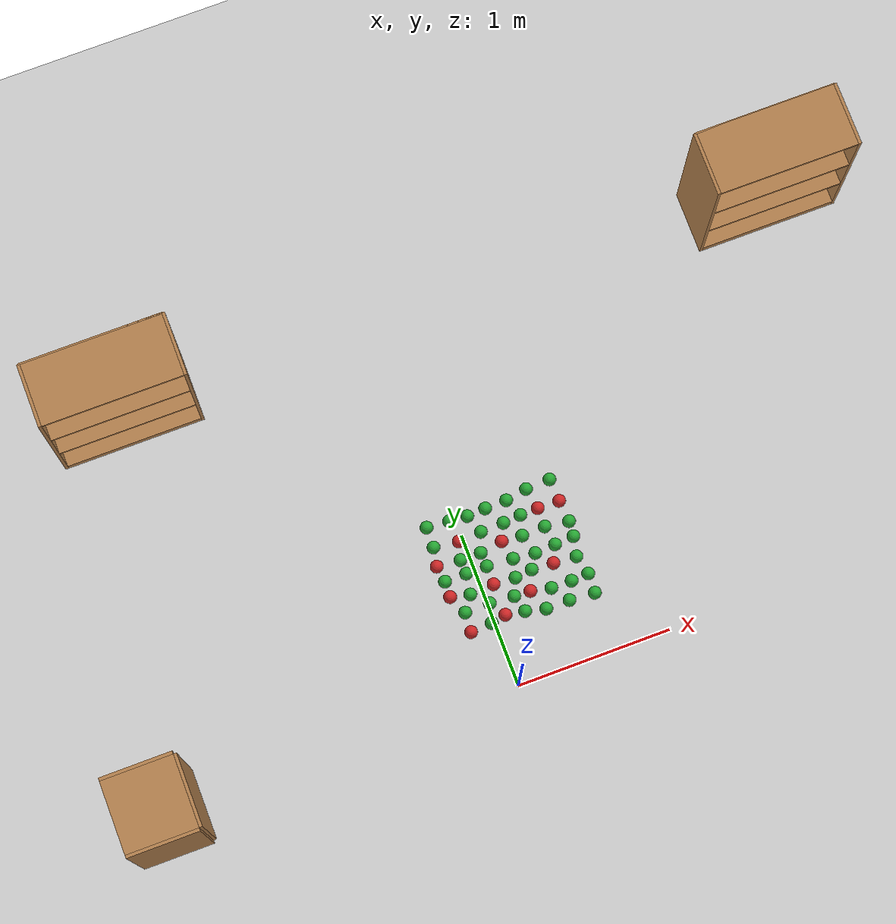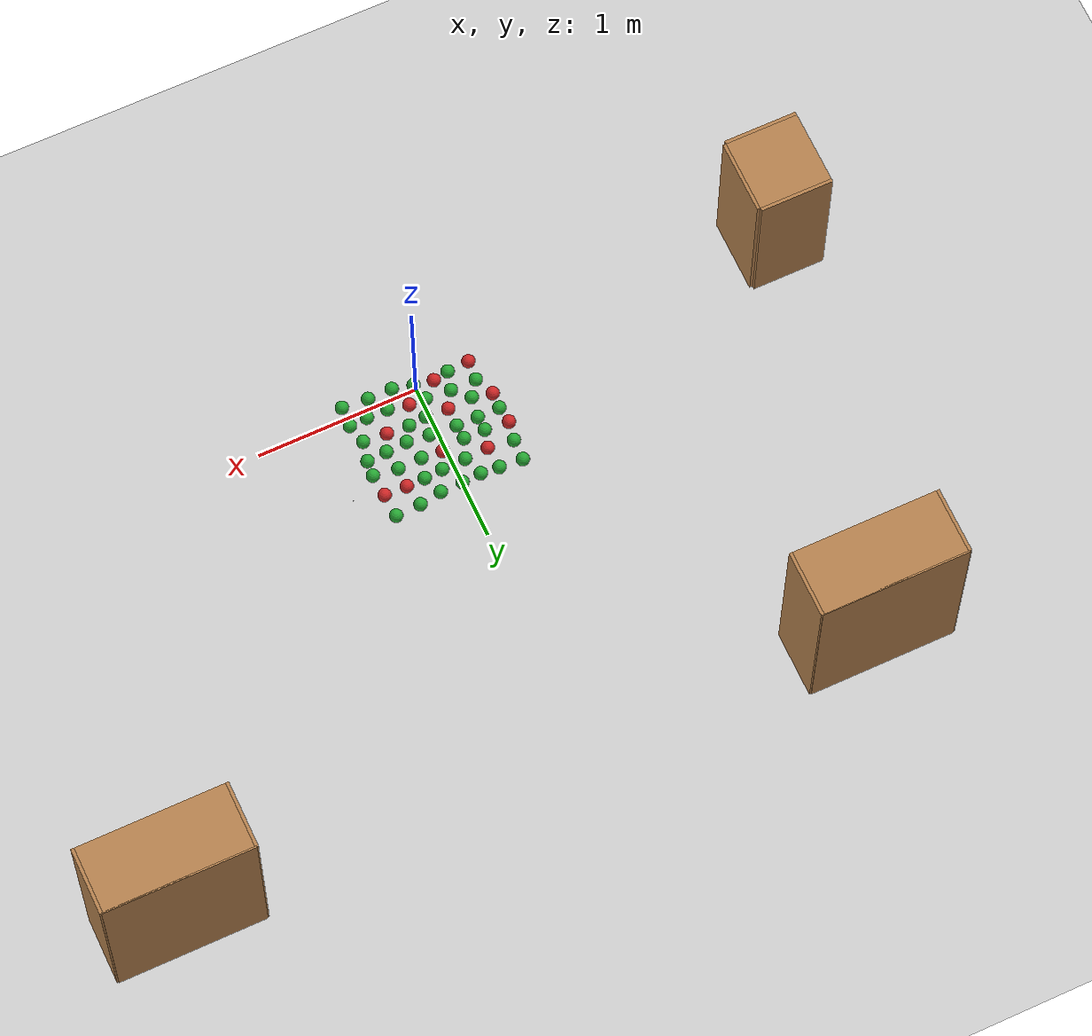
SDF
<sdf version="1.6">
 <world name="default">
  <light name="sun" type="directional">
   <pose>0 0 10 0 -0 0</pose>
   <diffuse>0.8 0.8 0.8 1</diffuse>
   <specular>0.2 0.2 0.2 1</specular>
   <attenuation>
    <range>1000</range>
    <constant>0.9</constant>
    <linear>0.01</linear>
    <quadratic>0.001</quadratic>
   </attenuation>
   <direction>-0.5 0.1 -0.9</direction>
  </light>
  <model name="ground_plane">
   <static>1</static>
   <link name="link">
    <collision name="collision">
     <geometry><plane><normal>0 0 1</normal><size>100 100</size></plane></geometry>
     <surface><friction><ode><mu>100</mu><mu2>50</mu2></ode></friction></surface>
    </collision>
    <visual name="visual">
     <cast_shadows>0</cast_shadows>
     <geometry><plane><normal>0 0 1</normal><size>100 100</size></plane></geometry>
     <material>
      <script><uri>file://media/materials/scripts/gazebo.material</uri><name>Gazebo/Grey</name></script>
     </material>
    </visual>
   </link>
  </model>
  <gravity>0 0 -9.8</gravity>
  <magnetic_field>6e-06 2.3e-05 -4.2e-05</magnetic_field>
  <atmosphere type="adiabatic"/>
  <physics name="default_physics" default="0" type="ode">
   <max_step_size>0.001</max_step_size>
   <real_time_factor>1</real_time_factor>
   <real_time_update_rate>1000</real_time_update_rate>
  </physics>
  <scene><ambient>0.4 0.4 0.4 1</ambient><background>0.7 0.7 0.7 1</background><shadows>1</shadows></scene>
  <audio><device>default</device></audio>
  <spherical_coordinates>
   <surface_model>EARTH_WGS84</surface_model>
   <latitude_deg>0</latitude_deg>
   <longitude_deg>0</longitude_deg>
   <elevation>0</elevation>
   <heading_deg>0</heading_deg>
  </spherical_coordinates>
  <model name="cabinet">
   <static>1</static>
   <link name="cabinet_bottom_plate">
    <inertial>
     <pose>0 0 -1 0 -0 0</pose>
     <inertia><ixx>2.05</ixx><ixy>0</ixy><ixz>0</ixz><iyy>2.05</iyy><iyz>0</iyz><izz>2.05</izz></inertia>
     <mass>25</mass>
    </inertial>
    <collision name="cabinet_bottom_plate_geom">
     <pose>0 0 0.01 0 -0 0</pose>
     <geometry><box><size>0.45 0.45 0.02</size></box></geometry>
    </collision>
    <visual name="cabinet_bottom_plate_geom_visual">
     <pose>0 0 0.01 0 -0 0</pose>
     <geometry><box><size>0.45 0.45 0.02</size></box></geometry>
     <material>
      <script><uri>file://media/materials/scripts/gazebo.material</uri><name>Gazebo/Wood</name></script>
     </material>
    </visual>
    <collision name="cabinet_bottom_plate_geom_cabinet_back_plate">
     <pose>0.235 0 0.51 0 -0 0</pose>
     <geometry><box><size>0.02 0.45 1.02</size></box></geometry>
    </collision>
    <visual name="cabinet_bottom_plate_geom_cabinet_back_plate_visual">
     <pose>0.235 0 0.51 0 -0 0</pose>
     <geometry><box><size>0.02 0.45 1.02</size></box></geometry>
     <material>
      <script><uri>file://media/materials/scripts/gazebo.material</uri><name>Gazebo/Wood</name></script>
     </material>
    </visual>
    <collision name="cabinet_bottom_plate_geom_cabinet_left_plate">
     <pose>0 0.235 0.51 0 -0 0</pose>
     <geometry><box><size>0.45 0.02 1.02</size></box></geometry>
    </collision>
    <visual name="cabinet_bottom_plate_geom_cabinet_left_plate_visual">
     <pose>0 0.235 0.51 0 -0 0</pose>
     <geometry><box><size>0.45 0.02 1.02</size></box></geometry>
     <material>
      <script><uri>file://media/materials/scripts/gazebo.material</uri><name>Gazebo/Wood</name></script>
     </material>
    </visual>
    <collision name="cabinet_bottom_plate_geom_cabinet_middle_plate">
     <pose>0 0 0.51 0 -0 0</pose>
     <geometry><box><size>0.45 0.45 0.02</size></box></geometry>
    </collision>
    <visual name="cabinet_bottom_plate_geom_cabinet_middle_plate_visual">
     <pose>0 0 0.51 0 -0 0</pose>
     <geometry><box><size>0.45 0.45 0.02</size></box></geometry>
     <material>
      <script><uri>file://media/materials/scripts/gazebo.material</uri><name>Gazebo/Wood</name></script>
     </material>
    </visual>
    <collision name="cabinet_bottom_plate_geom_cabinet_right_plate">
     <pose>0 -0.235 0.51 0 -0 0</pose>
     <geometry><box><size>0.45 0.02 1.02</size></box></geometry>
    </collision>
    <visual name="cabinet_bottom_plate_geom_cabinet_right_plate_visual">
     <pose>0 -0.235 0.51 0 -0 0</pose>
     <geometry><box><size>0.45 0.02 1.02</size></box></geometry>
     <material>
      <script><uri>file://media/materials/scripts/gazebo.material</uri><name>Gazebo/Wood</name></script>
     </material>
    </visual>
    <collision name="cabinet_bottom_plate_geom_cabinet_top_plate">
     <pose>0 0 1.01 0 -0 0</pose>
     <geometry><box><size>0.45 0.45 0.02</size></box></geometry>
    </collision>
    <visual name="cabinet_bottom_plate_geom_cabinet_top_plate_visual">
     <pose>0 0 1.01 0 -0 0</pose>
     <geometry><box><size>0.45 0.45 0.02</size></box></geometry>
     <material>
      <script><uri>file://media/materials/scripts/gazebo.material</uri><name>Gazebo/Wood</name></script>
     </material>
    </visual>
   </link>
   <pose>-2.29685 -0.011015 0 0 -0 0</pose>
  </model>
  <model name="bookshelf">
   <static>1</static>
   <link name="link">
    <inertial><mass>1</mass></inertial>
    <collision name="back">
     <pose>0 0.005 0.6 0 -0 0</pose>
     <geometry><box><size>0.9 0.01 1.2</size></box></geometry>
    </collision>
    <visual name="visual1">
     <pose>0 0.005 0.6 0 -0 0</pose>
     <geometry><box><size>0.9 0.01 1.2</size></box></geometry>
     <material>
      <script><uri>file://media/materials/scripts/gazebo.material</uri><name>Gazebo/Wood</name></script>
     </material>
    </visual>
    <collision name="left_side">
     <pose>0.45 -0.195 0.6 0 -0 0</pose>
     <geometry><box><size>0.02 0.4 1.2</size></box></geometry>
    </collision>
    <visual name="visual2">
     <pose>0.45 -0.195 0.6 0 -0 0</pose>
     <geometry><box><size>0.02 0.4 1.2</size></box></geometry>
     <material>
      <script><uri>file://media/materials/scripts/gazebo.material</uri><name>Gazebo/Wood</name></script>
     </material>
    </visual>
    <collision name="right_side">
     <pose>-0.45 -0.195 0.6 0 -0 0</pose>
     <geometry><box><size>0.02 0.4 1.2</size></box></geometry>
    </collision>
    <visual name="visual3">
     <pose>-0.45 -0.195 0.6 0 -0 0</pose>
     <geometry><box><size>0.02 0.4 1.2</size></box></geometry>
     <material>
      <script><uri>file://media/materials/scripts/gazebo.material</uri><name>Gazebo/Wood</name></script>
     </material>
    </visual>
    <collision name="bottom">
     <pose>0 -0.195 0.03 0 -0 0</pose>
     <geometry><box><size>0.88 0.4 0.06</size></box></geometry>
    </collision>
    <visual name="visual4">
     <pose>0 -0.195 0.03 0 -0 0</pose>
     <geometry><box><size>0.88 0.4 0.06</size></box></geometry>
     <material>
      <script><uri>file://media/materials/scripts/gazebo.material</uri><name>Gazebo/Wood</name></script>
     </material>
    </visual>
    <collision name="top">
     <pose>0 -0.195 1.19 0 -0 0</pose>
     <geometry><box><size>0.88 0.4 0.02</size></box></geometry>
    </collision>
    <visual name="visual5">
     <pose>0 -0.195 1.19 0 -0 0</pose>
     <geometry><box><size>0.88 0.4 0.02</size></box></geometry>
     <material>
      <script><uri>file://media/materials/scripts/gazebo.material</uri><name>Gazebo/Wood</name></script>
     </material>
    </visual>
    <collision name="low_shelf">
     <pose>0 -0.195 0.43 0 -0 0</pose>
     <geometry><box><size>0.88 0.4 0.02</size></box></geometry>
    </collision>
    <visual name="visual6">
     <pose>0 -0.195 0.43 0 -0 0</pose>
     <geometry><box><size>0.88 0.4 0.02</size></box></geometry>
     <material>
      <script><uri>file://media/materials/scripts/gazebo.material</uri><name>Gazebo/Wood</name></script>
     </material>
    </visual>
    <collision name="high_shelf">
     <pose>0 -0.195 0.8 0 -0 0</pose>
     <geometry><box><size>0.88 0.4 0.02</size></box></geometry>
    </collision>
    <visual name="visual7">
     <pose>0 -0.195 0.8 0 -0 0</pose>
     <geometry><box><size>0.88 0.4 0.02</size></box></geometry>
     <material>
      <script><uri>file://media/materials/scripts/gazebo.material</uri><name>Gazebo/Wood</name></script>
     </material>
    </visual>
   </link>
   <pose>-1.70945 2.65382 0 0 -0 0</pose>
  </model>
  <model name="bookshelf_0">
   <static>1</static>
   <link name="link">
    <inertial><mass>1</mass></inertial>
    <collision name="back">
     <pose>0 0.005 0.6 0 -0 0</pose>
     <geometry><box><size>0.9 0.01 1.2</size></box></geometry>
    </collision>
    <visual name="visual1">
     <pose>0 0.005 0.6 0 -0 0</pose>
     <geometry><box><size>0.9 0.01 1.2</size></box></geometry>
     <material>
      <script><uri>file://media/materials/scripts/gazebo.material</uri><name>Gazebo/Wood</name></script>
     </material>
    </visual>
    <collision name="left_side">
     <pose>0.45 -0.195 0.6 0 -0 0</pose>
     <geometry><box><size>0.02 0.4 1.2</size></box></geometry>
    </collision>
    <visual name="visual2">
     <pose>0.45 -0.195 0.6 0 -0 0</pose>
     <geometry><box><size>0.02 0.4 1.2</size></box></geometry>
     <material>
      <script><uri>file://media/materials/scripts/gazebo.material</uri><name>Gazebo/Wood</name></script>
     </material>
    </visual>
    <collision name="right_side">
     <pose>-0.45 -0.195 0.6 0 -0 0</pose>
     <geometry><box><size>0.02 0.4 1.2</size></box></geometry>
    </collision>
    <visual name="visual3">
     <pose>-0.45 -0.195 0.6 0 -0 0</pose>
     <geometry><box><size>0.02 0.4 1.2</size></box></geometry>
     <material>
      <script><uri>file://media/materials/scripts/gazebo.material</uri><name>Gazebo/Wood</name></script>
     </material>
    </visual>
    <collision name="bottom">
     <pose>0 -0.195 0.03 0 -0 0</pose>
     <geometry><box><size>0.88 0.4 0.06</size></box></geometry>
    </collision>
    <visual name="visual4">
     <pose>0 -0.195 0.03 0 -0 0</pose>
     <geometry><box><size>0.88 0.4 0.06</size></box></geometry>
     <material>
      <script><uri>file://media/materials/scripts/gazebo.material</uri><name>Gazebo/Wood</name></script>
     </material>
    </visual>
    <collision name="top">
     <pose>0 -0.195 1.19 0 -0 0</pose>
     <geometry><box><size>0.88 0.4 0.02</size></box></geometry>
    </collision>
    <visual name="visual5">
     <pose>0 -0.195 1.19 0 -0 0</pose>
     <geometry><box><size>0.88 0.4 0.02</size></box></geometry>
     <material>
      <script><uri>file://media/materials/scripts/gazebo.material</uri><name>Gazebo/Wood</name></script>
     </material>
    </visual>
    <collision name="low_shelf">
     <pose>0 -0.195 0.43 0 -0 0</pose>
     <geometry><box><size>0.88 0.4 0.02</size></box></geometry>
    </collision>
    <visual name="visual6">
     <pose>0 -0.195 0.43 0 -0 0</pose>
     <geometry><box><size>0.88 0.4 0.02</size></box></geometry>
     <material>
      <script><uri>file://media/materials/scripts/gazebo.material</uri><name>Gazebo/Wood</name></script>
     </material>
    </visual>
    <collision name="high_shelf">
     <pose>0 -0.195 0.8 0 -0 0</pose>
     <geometry><box><size>0.88 0.4 0.02</size></box></geometry>
    </collision>
    <visual name="visual7">
     <pose>0 -0.195 0.8 0 -0 0</pose>
     <geometry><box><size>0.88 0.4 0.02</size></box></geometry>
     <material>
      <script><uri>file://media/materials/scripts/gazebo.material</uri><name>Gazebo/Wood</name></script>
     </material>
    </visual>
   </link>
   <pose>2.52008 2.58706 0 0 -0 0</pose>
  </model>
  <model name="ball_bearing">
   <link name="link">
    <pose>0 0 0.003 0 -0 0</pose>
    <inertial>
     <mass>0.0011</mass>
     <inertia>
      <ixx>3.96e-09</ixx>
      <ixy>0</ixy>
      <ixz>0</ixz>
      <iyy>3.96e-09</iyy>
      <iyz>0</iyz>
      <izz>3.96e-09</izz>
     </inertia>
    </inertial>
    <collision name="collision">
     <geometry><sphere><radius>0.003</radius></sphere></geometry>
     <surface>
      <contact>
       <poissons_ratio>0.305</poissons_ratio>
       <elastic_modulus>2e+11</elastic_modulus>
       <ode><kp>100000</kp><kd>100</kd><max_vel>100</max_vel><min_depth>0.001</min_depth></ode>
      </contact>
      <friction>
       <torsional>
        <coefficient>1</coefficient>
        <use_patch_radius>0</use_patch_radius>
        <surface_radius>0.01</surface_radius>
       </torsional>
      </friction>
     </surface>
    </collision>
    <visual name="visual">
     <geometry><sphere><radius>0.003</radius></sphere></geometry>
     <material>
      <script><uri>file://media/materials/scripts/gazebo.material</uri><name>Gazebo/Grey</name></script>
     </material>
    </visual>
    <velocity_decay><linear>0</linear><angular>0.005</angular></velocity_decay>
   </link>
   <pose>0.615587 0.485101 -0.001 0 -0 0</pose>
  </model>
  <model name="green_apple">
   <link name="link">
    <inertial>
     <mass>1</mass>
     <inertia><ixx>0.1</ixx><ixy>0</ixy><ixz>0</ixz><iyy>0.1</iyy><iyz>0</iyz><izz>0.1</izz></inertia>
    </inertial>
    <visual name="visual">
     <geometry><sphere><radius>0.04</radius></sphere></geometry>
     <material>
      <script><name>Gazebo/Green</name><uri>file://media/materials/scripts/gazebo.material</uri></script>
      <shader type="vertex"><normal_map>__default__</normal_map></shader>
      <ambient>0 1 0 1</ambient>
      <diffuse>0.7 0.7 0.7 1</diffuse>
      <specular>0.01 0.01 0.01 1</specular>
      <emissive>0 0 0 1</emissive>
     </material>
    </visual>
    <collision name="collision">
     <geometry><sphere><radius>0.04</radius></sphere></geometry>
     <surface>
      <friction>
       <ode><mu>1</mu><mu2>1</mu2><fdir1>0 0 0</fdir1><slip1>0</slip1><slip2>0</slip2></ode>
       <torsional>
        <coefficient>1</coefficient>
        <patch_radius>0</patch_radius>
        <surface_radius>0</surface_radius>
        <use_patch_radius>1</use_patch_radius>
        <ode><slip>0</slip></ode>
       </torsional>
      </friction>
      <bounce><restitution_coefficient>0</restitution_coefficient><threshold>1e+06</threshold></bounce>
      <contact>
       <collide_without_contact>0</collide_without_contact>
       <collide_without_contact_bitmask>1</collide_without_contact_bitmask>
       <collide_bitmask>1</collide_bitmask>
       <ode>
        <soft_cfm>0</soft_cfm>
        <soft_erp>0.2</soft_erp>
        <kp>1e+13</kp>
        <kd>1</kd>
        <max_vel>0.01</max_vel>
        <min_depth>0</min_depth>
       </ode>
       <bullet>
        <split_impulse>1</split_impulse>
        <split_impulse_penetration_threshold>-0.01</split_impulse_penetration_threshold>
        <soft_cfm>0</soft_cfm>
        <soft_erp>0.2</soft_erp>
        <kp>1e+13</kp>
        <kd>1</kd>
       </bullet>
      </contact>
     </surface>
    </collision>
   </link>
   <static>0</static>
   <pose>0.551902 0.999522 0.815 0 -0 0</pose>
  </model>
  <model name="red_apple">
   <link name="link">
    <inertial>
     <mass>1</mass>
     <inertia><ixx>0.1</ixx><ixy>0</ixy><ixz>0</ixz><iyy>0.1</iyy><iyz>0</iyz><izz>0.1</izz></inertia>
    </inertial>
    <visual name="visual">
     <geometry><sphere><radius>0.04</radius></sphere></geometry>
     <material>
      <script><name>Gazebo/Red</name><uri>file://media/materials/scripts/gazebo.material</uri></script>
      <shader type="vertex"><normal_map>__default__</normal_map></shader>
      <ambient>1 0 0 1</ambient>
      <diffuse>0.7 0.7 0.7 1</diffuse>
      <specular>0.01 0.01 0.01 1</specular>
      <emissive>0 0 0 1</emissive>
     </material>
    </visual>
    <collision name="collision">
     <geometry><sphere><radius>0.04</radius></sphere></geometry>
     <surface>
      <friction>
       <ode><mu>1</mu><mu2>1</mu2><fdir1>0 0 0</fdir1><slip1>0</slip1><slip2>0</slip2></ode>
       <torsional>
        <coefficient>1</coefficient>
        <patch_radius>0</patch_radius>
        <surface_radius>0</surface_radius>
        <use_patch_radius>1</use_patch_radius>
        <ode><slip>0</slip></ode>
       </torsional>
      </friction>
      <bounce><restitution_coefficient>0</restitution_coefficient><threshold>1e+06</threshold></bounce>
      <contact>
       <collide_without_contact>0</collide_without_contact>
       <collide_without_contact_bitmask>1</collide_without_contact_bitmask>
       <collide_bitmask>1</collide_bitmask>
       <ode>
        <soft_cfm>0</soft_cfm>
        <soft_erp>0.2</soft_erp>
        <kp>1e+13</kp>
        <kd>1</kd>
        <max_vel>0.01</max_vel>
        <min_depth>0</min_depth>
       </ode>
       <bullet>
        <split_impulse>1</split_impulse>
        <split_impulse_penetration_threshold>-0.01</split_impulse_penetration_threshold>
        <soft_cfm>0</soft_cfm>
        <soft_erp>0.2</soft_erp>
        <kp>1e+13</kp>
        <kd>1</kd>
       </bullet>
      </contact>
     </surface>
    </collision>
   </link>
   <static>0</static>
   <pose>0.559639 0.858674 0.815 0 -0 0</pose>
  </model>
  <model name="red_apple_clone">
   <link name="link">
    <inertial>
     <mass>1</mass>
     <inertia><ixx>0.1</ixx><ixy>0</ixy><ixz>0</ixz><iyy>0.1</iyy><iyz>0</iyz><izz>0.1</izz></inertia>
    </inertial>
    <visual name="visual">
     <geometry><sphere><radius>0.04</radius></sphere></geometry>
     <material>
      <script><name>Gazebo/Red</name><uri>file://media/materials/scripts/gazebo.material</uri></script>
      <shader type="vertex"><normal_map>__default__</normal_map></shader>
      <ambient>1 0 0 1</ambient>
      <diffuse>0.7 0.7 0.7 1</diffuse>
      <specular>0.01 0.01 0.01 1</specular>
      <emissive>0 0 0 1</emissive>
     </material>
    </visual>
    <collision name="collision">
     <geometry><sphere><radius>0.04</radius></sphere></geometry>
     <surface>
      <friction>
       <ode><mu>1</mu><mu2>1</mu2><fdir1>0 0 0</fdir1><slip1>0</slip1><slip2>0</slip2></ode>
       <torsional>
        <coefficient>1</coefficient>
        <patch_radius>0</patch_radius>
        <surface_radius>0</surface_radius>
        <use_patch_radius>1</use_patch_radius>
        <ode><slip>0</slip></ode>
       </torsional>
      </friction>
      <bounce><restitution_coefficient>0</restitution_coefficient><threshold>1e+06</threshold></bounce>
      <contact>
       <collide_without_contact>0</collide_without_contact>
       <collide_without_contact_bitmask>1</collide_without_contact_bitmask>
       <collide_bitmask>1</collide_bitmask>
       <ode>
        <soft_cfm>0</soft_cfm>
        <soft_erp>0.2</soft_erp>
        <kp>1e+13</kp>
        <kd>1</kd>
        <max_vel>0.01</max_vel>
        <min_depth>0</min_depth>
       </ode>
       <bullet>
        <split_impulse>1</split_impulse>
        <split_impulse_penetration_threshold>-0.01</split_impulse_penetration_threshold>
        <soft_cfm>0</soft_cfm>
        <soft_erp>0.2</soft_erp>
        <kp>1e+13</kp>
        <kd>1</kd>
       </bullet>
      </contact>
     </surface>
    </collision>
   </link>
   <static>0</static>
   <pose>0.424941 0.861418 0.815 0 -0 0</pose>
  </model>
  <model name="green_apple_clone">
   <link name="link">
    <inertial>
     <mass>1</mass>
     <inertia><ixx>0.1</ixx><ixy>0</ixy><ixz>0</ixz><iyy>0.1</iyy><iyz>0</iyz><izz>0.1</izz></inertia>
    </inertial>
    <visual name="visual">
     <geometry><sphere><radius>0.04</radius></sphere></geometry>
     <material>
      <script><name>Gazebo/Green</name><uri>file://media/materials/scripts/gazebo.material</uri></script>
      <shader type="vertex"><normal_map>__default__</normal_map></shader>
      <ambient>0 1 0 1</ambient>
      <diffuse>0.7 0.7 0.7 1</diffuse>
      <specular>0.01 0.01 0.01 1</specular>
      <emissive>0 0 0 1</emissive>
     </material>
    </visual>
    <collision name="collision">
     <geometry><sphere><radius>0.04</radius></sphere></geometry>
     <surface>
      <friction>
       <ode><mu>1</mu><mu2>1</mu2><fdir1>0 0 0</fdir1><slip1>0</slip1><slip2>0</slip2></ode>
       <torsional>
        <coefficient>1</coefficient>
        <patch_radius>0</patch_radius>
        <surface_radius>0</surface_radius>
        <use_patch_radius>1</use_patch_radius>
        <ode><slip>0</slip></ode>
       </torsional>
      </friction>
      <bounce><restitution_coefficient>0</restitution_coefficient><threshold>1e+06</threshold></bounce>
      <contact>
       <collide_without_contact>0</collide_without_contact>
       <collide_without_contact_bitmask>1</collide_without_contact_bitmask>
       <collide_bitmask>1</collide_bitmask>
       <ode>
        <soft_cfm>0</soft_cfm>
        <soft_erp>0.2</soft_erp>
        <kp>1e+13</kp>
        <kd>1</kd>
        <max_vel>0.01</max_vel>
        <min_depth>0</min_depth>
       </ode>
       <bullet>
        <split_impulse>1</split_impulse>
        <split_impulse_penetration_threshold>-0.01</split_impulse_penetration_threshold>
        <soft_cfm>0</soft_cfm>
        <soft_erp>0.2</soft_erp>
        <kp>1e+13</kp>
        <kd>1</kd>
       </bullet>
      </contact>
     </surface>
    </collision>
   </link>
   <static>0</static>
   <pose>0.400447 0.993653 0.815 0 -0 0</pose>
  </model>
  <model name="green_apple_clone_0">
   <link name="link">
    <inertial>
     <mass>1</mass>
     <inertia><ixx>0.1</ixx><ixy>0</ixy><ixz>0</ixz><iyy>0.1</iyy><iyz>0</iyz><izz>0.1</izz></inertia>
    </inertial>
    <visual name="visual">
     <geometry><sphere><radius>0.04</radius></sphere></geometry>
     <material>
      <script><name>Gazebo/Green</name><uri>file://media/materials/scripts/gazebo.material</uri></script>
      <shader type="vertex"><normal_map>__default__</normal_map></shader>
      <ambient>0 1 0 1</ambient>
      <diffuse>0.7 0.7 0.7 1</diffuse>
      <specular>0.01 0.01 0.01 1</specular>
      <emissive>0 0 0 1</emissive>
     </material>
    </visual>
    <collision name="collision">
     <geometry><sphere><radius>0.04</radius></sphere></geometry>
     <surface>
      <friction>
       <ode><mu>1</mu><mu2>1</mu2><fdir1>0 0 0</fdir1><slip1>0</slip1><slip2>0</slip2></ode>
       <torsional>
        <coefficient>1</coefficient>
        <patch_radius>0</patch_radius>
        <surface_radius>0</surface_radius>
        <use_patch_radius>1</use_patch_radius>
        <ode><slip>0</slip></ode>
       </torsional>
      </friction>
      <bounce><restitution_coefficient>0</restitution_coefficient><threshold>1e+06</threshold></bounce>
      <contact>
       <collide_without_contact>0</collide_without_contact>
       <collide_without_contact_bitmask>1</collide_without_contact_bitmask>
       <collide_bitmask>1</collide_bitmask>
       <ode>
        <soft_cfm>0</soft_cfm>
        <soft_erp>0.2</soft_erp>
        <kp>1e+13</kp>
        <kd>1</kd>
        <max_vel>0.01</max_vel>
        <min_depth>0</min_depth>
       </ode>
       <bullet>
        <split_impulse>1</split_impulse>
        <split_impulse_penetration_threshold>-0.01</split_impulse_penetration_threshold>
        <soft_cfm>0</soft_cfm>
        <soft_erp>0.2</soft_erp>
        <kp>1e+13</kp>
        <kd>1</kd>
       </bullet>
      </contact>
     </surface>
    </collision>
   </link>
   <static>0</static>
   <pose>0.423986 0.743621 0.815 0 -0 0</pose>
  </model>
  <model name="green_apple_clone_1">
   <link name="link">
    <inertial>
     <mass>1</mass>
     <inertia><ixx>0.1</ixx><ixy>0</ixy><ixz>0</ixz><iyy>0.1</iyy><iyz>0</iyz><izz>0.1</izz></inertia>
    </inertial>
    <visual name="visual">
     <geometry><sphere><radius>0.04</radius></sphere></geometry>
     <material>
      <script><name>Gazebo/Green</name><uri>file://media/materials/scripts/gazebo.material</uri></script>
      <shader type="vertex"><normal_map>__default__</normal_map></shader>
      <ambient>0 1 0 1</ambient>
      <diffuse>0.7 0.7 0.7 1</diffuse>
      <specular>0.01 0.01 0.01 1</specular>
      <emissive>0 0 0 1</emissive>
     </material>
    </visual>
    <collision name="collision">
     <geometry><sphere><radius>0.04</radius></sphere></geometry>
     <surface>
      <friction>
       <ode><mu>1</mu><mu2>1</mu2><fdir1>0 0 0</fdir1><slip1>0</slip1><slip2>0</slip2></ode>
       <torsional>
        <coefficient>1</coefficient>
        <patch_radius>0</patch_radius>
        <surface_radius>0</surface_radius>
        <use_patch_radius>1</use_patch_radius>
        <ode><slip>0</slip></ode>
       </torsional>
      </friction>
      <bounce><restitution_coefficient>0</restitution_coefficient><threshold>1e+06</threshold></bounce>
      <contact>
       <collide_without_contact>0</collide_without_contact>
       <collide_without_contact_bitmask>1</collide_without_contact_bitmask>
       <collide_bitmask>1</collide_bitmask>
       <ode>
        <soft_cfm>0</soft_cfm>
        <soft_erp>0.2</soft_erp>
        <kp>1e+13</kp>
        <kd>1</kd>
        <max_vel>0.01</max_vel>
        <min_depth>0</min_depth>
       </ode>
       <bullet>
        <split_impulse>1</split_impulse>
        <split_impulse_penetration_threshold>-0.01</split_impulse_penetration_threshold>
        <soft_cfm>0</soft_cfm>
        <soft_erp>0.2</soft_erp>
        <kp>1e+13</kp>
        <kd>1</kd>
       </bullet>
      </contact>
     </surface>
    </collision>
   </link>
   <static>0</static>
   <pose>0.570669 0.723231 0.815 0 -0 0</pose>
  </model>
  <model name="green_apple_clone_2">
   <link name="link">
    <inertial>
     <mass>1</mass>
     <inertia><ixx>0.1</ixx><ixy>0</ixy><ixz>0</ixz><iyy>0.1</iyy><iyz>0</iyz><izz>0.1</izz></inertia>
    </inertial>
    <visual name="visual">
     <geometry><sphere><radius>0.04</radius></sphere></geometry>
     <material>
      <script><name>Gazebo/Green</name><uri>file://media/materials/scripts/gazebo.material</uri></script>
      <shader type="vertex"><normal_map>__default__</normal_map></shader>
      <ambient>0 1 0 1</ambient>
      <diffuse>0.7 0.7 0.7 1</diffuse>
      <specular>0.01 0.01 0.01 1</specular>
      <emissive>0 0 0 1</emissive>
     </material>
    </visual>
    <collision name="collision">
     <geometry><sphere><radius>0.04</radius></sphere></geometry>
     <surface>
      <friction>
       <ode><mu>1</mu><mu2>1</mu2><fdir1>0 0 0</fdir1><slip1>0</slip1><slip2>0</slip2></ode>
       <torsional>
        <coefficient>1</coefficient>
        <patch_radius>0</patch_radius>
        <surface_radius>0</surface_radius>
        <use_patch_radius>1</use_patch_radius>
        <ode><slip>0</slip></ode>
       </torsional>
      </friction>
      <bounce><restitution_coefficient>0</restitution_coefficient><threshold>1e+06</threshold></bounce>
      <contact>
       <collide_without_contact>0</collide_without_contact>
       <collide_without_contact_bitmask>1</collide_without_contact_bitmask>
       <collide_bitmask>1</collide_bitmask>
       <ode>
        <soft_cfm>0</soft_cfm>
        <soft_erp>0.2</soft_erp>
        <kp>1e+13</kp>
        <kd>1</kd>
        <max_vel>0.01</max_vel>
        <min_depth>0</min_depth>
       </ode>
       <bullet>
        <split_impulse>1</split_impulse>
        <split_impulse_penetration_threshold>-0.01</split_impulse_penetration_threshold>
        <soft_cfm>0</soft_cfm>
        <soft_erp>0.2</soft_erp>
        <kp>1e+13</kp>
        <kd>1</kd>
       </bullet>
      </contact>
     </surface>
    </collision>
   </link>
   <static>0</static>
   <pose>-0.233826 0.981757 0.815 0 -0 0</pose>
  </model>
  <model name="green_apple_clone_3">
   <link name="link">
    <inertial>
     <mass>1</mass>
     <inertia><ixx>0.1</ixx><ixy>0</ixy><ixz>0</ixz><iyy>0.1</iyy><iyz>0</iyz><izz>0.1</izz></inertia>
    </inertial>
    <visual name="visual">
     <geometry><sphere><radius>0.04</radius></sphere></geometry>
     <material>
      <script><name>Gazebo/Green</name><uri>file://media/materials/scripts/gazebo.material</uri></script>
      <shader type="vertex"><normal_map>__default__</normal_map></shader>
      <ambient>0 1 0 1</ambient>
      <diffuse>0.7 0.7 0.7 1</diffuse>
      <specular>0.01 0.01 0.01 1</specular>
      <emissive>0 0 0 1</emissive>
     </material>
    </visual>
    <collision name="collision">
     <geometry><sphere><radius>0.04</radius></sphere></geometry>
     <surface>
      <friction>
       <ode><mu>1</mu><mu2>1</mu2><fdir1>0 0 0</fdir1><slip1>0</slip1><slip2>0</slip2></ode>
       <torsional>
        <coefficient>1</coefficient>
        <patch_radius>0</patch_radius>
        <surface_radius>0</surface_radius>
        <use_patch_radius>1</use_patch_radius>
        <ode><slip>0</slip></ode>
       </torsional>
      </friction>
      <bounce><restitution_coefficient>0</restitution_coefficient><threshold>1e+06</threshold></bounce>
      <contact>
       <collide_without_contact>0</collide_without_contact>
       <collide_without_contact_bitmask>1</collide_without_contact_bitmask>
       <collide_bitmask>1</collide_bitmask>
       <ode>
        <soft_cfm>0</soft_cfm>
        <soft_erp>0.2</soft_erp>
        <kp>1e+13</kp>
        <kd>1</kd>
        <max_vel>0.01</max_vel>
        <min_depth>0</min_depth>
       </ode>
       <bullet>
        <split_impulse>1</split_impulse>
        <split_impulse_penetration_threshold>-0.01</split_impulse_penetration_threshold>
        <soft_cfm>0</soft_cfm>
        <soft_erp>0.2</soft_erp>
        <kp>1e+13</kp>
        <kd>1</kd>
       </bullet>
      </contact>
     </surface>
    </collision>
   </link>
   <static>0</static>
   <pose>-0.094552 0.971199 0.815 0 -0 0</pose>
  </model>
  <model name="green_apple_clone_4">
   <link name="link">
    <inertial>
     <mass>1</mass>
     <inertia><ixx>0.1</ixx><ixy>0</ixy><ixz>0</ixz><iyy>0.1</iyy><iyz>0</iyz><izz>0.1</izz></inertia>
    </inertial>
    <visual name="visual">
     <geometry><sphere><radius>0.04</radius></sphere></geometry>
     <material>
      <script><name>Gazebo/Green</name><uri>file://media/materials/scripts/gazebo.material</uri></script>
      <shader type="vertex"><normal_map>__default__</normal_map></shader>
      <ambient>0 1 0 1</ambient>
      <diffuse>0.7 0.7 0.7 1</diffuse>
      <specular>0.01 0.01 0.01 1</specular>
      <emissive>0 0 0 1</emissive>
     </material>
    </visual>
    <collision name="collision">
     <geometry><sphere><radius>0.04</radius></sphere></geometry>
     <surface>
      <friction>
       <ode><mu>1</mu><mu2>1</mu2><fdir1>0 0 0</fdir1><slip1>0</slip1><slip2>0</slip2></ode>
       <torsional>
        <coefficient>1</coefficient>
        <patch_radius>0</patch_radius>
        <surface_radius>0</surface_radius>
        <use_patch_radius>1</use_patch_radius>
        <ode><slip>0</slip></ode>
       </torsional>
      </friction>
      <bounce><restitution_coefficient>0</restitution_coefficient><threshold>1e+06</threshold></bounce>
      <contact>
       <collide_without_contact>0</collide_without_contact>
       <collide_without_contact_bitmask>1</collide_without_contact_bitmask>
       <collide_bitmask>1</collide_bitmask>
       <ode>
        <soft_cfm>0</soft_cfm>
        <soft_erp>0.2</soft_erp>
        <kp>1e+13</kp>
        <kd>1</kd>
        <max_vel>0.01</max_vel>
        <min_depth>0</min_depth>
       </ode>
       <bullet>
        <split_impulse>1</split_impulse>
        <split_impulse_penetration_threshold>-0.01</split_impulse_penetration_threshold>
        <soft_cfm>0</soft_cfm>
        <soft_erp>0.2</soft_erp>
        <kp>1e+13</kp>
        <kd>1</kd>
       </bullet>
      </contact>
     </surface>
    </collision>
   </link>
   <static>0</static>
   <pose>0.016604 0.962257 0.815 0 -0 0</pose>
  </model>
  <model name="green_apple_clone_5">
   <link name="link">
    <inertial>
     <mass>1</mass>
     <inertia><ixx>0.1</ixx><ixy>0</ixy><ixz>0</ixz><iyy>0.1</iyy><iyz>0</iyz><izz>0.1</izz></inertia>
    </inertial>
    <visual name="visual">
     <geometry><sphere><radius>0.04</radius></sphere></geometry>
     <material>
      <script><name>Gazebo/Green</name><uri>file://media/materials/scripts/gazebo.material</uri></script>
      <shader type="vertex"><normal_map>__default__</normal_map></shader>
      <ambient>0 1 0 1</ambient>
      <diffuse>0.7 0.7 0.7 1</diffuse>
      <specular>0.01 0.01 0.01 1</specular>
      <emissive>0 0 0 1</emissive>
     </material>
    </visual>
    <collision name="collision">
     <geometry><sphere><radius>0.04</radius></sphere></geometry>
     <surface>
      <friction>
       <ode><mu>1</mu><mu2>1</mu2><fdir1>0 0 0</fdir1><slip1>0</slip1><slip2>0</slip2></ode>
       <torsional>
        <coefficient>1</coefficient>
        <patch_radius>0</patch_radius>
        <surface_radius>0</surface_radius>
        <use_patch_radius>1</use_patch_radius>
        <ode><slip>0</slip></ode>
       </torsional>
      </friction>
      <bounce><restitution_coefficient>0</restitution_coefficient><threshold>1e+06</threshold></bounce>
      <contact>
       <collide_without_contact>0</collide_without_contact>
       <collide_without_contact_bitmask>1</collide_without_contact_bitmask>
       <collide_bitmask>1</collide_bitmask>
       <ode>
        <soft_cfm>0</soft_cfm>
        <soft_erp>0.2</soft_erp>
        <kp>1e+13</kp>
        <kd>1</kd>
        <max_vel>0.01</max_vel>
        <min_depth>0</min_depth>
       </ode>
       <bullet>
        <split_impulse>1</split_impulse>
        <split_impulse_penetration_threshold>-0.01</split_impulse_penetration_threshold>
        <soft_cfm>0</soft_cfm>
        <soft_erp>0.2</soft_erp>
        <kp>1e+13</kp>
        <kd>1</kd>
       </bullet>
      </contact>
     </surface>
    </collision>
   </link>
   <static>0</static>
   <pose>0.131703 0.968731 0.815 0 -0 0</pose>
  </model>
  <model name="green_apple_clone_6">
   <link name="link">
    <inertial>
     <mass>1</mass>
     <inertia><ixx>0.1</ixx><ixy>0</ixy><ixz>0</ixz><iyy>0.1</iyy><iyz>0</iyz><izz>0.1</izz></inertia>
    </inertial>
    <visual name="visual">
     <geometry><sphere><radius>0.04</radius></sphere></geometry>
     <material>
      <script><name>Gazebo/Green</name><uri>file://media/materials/scripts/gazebo.material</uri></script>
      <shader type="vertex"><normal_map>__default__</normal_map></shader>
      <ambient>0 1 0 1</ambient>
      <diffuse>0.7 0.7 0.7 1</diffuse>
      <specular>0.01 0.01 0.01 1</specular>
      <emissive>0 0 0 1</emissive>
     </material>
    </visual>
    <collision name="collision">
     <geometry><sphere><radius>0.04</radius></sphere></geometry>
     <surface>
      <friction>
       <ode><mu>1</mu><mu2>1</mu2><fdir1>0 0 0</fdir1><slip1>0</slip1><slip2>0</slip2></ode>
       <torsional>
        <coefficient>1</coefficient>
        <patch_radius>0</patch_radius>
        <surface_radius>0</surface_radius>
        <use_patch_radius>1</use_patch_radius>
        <ode><slip>0</slip></ode>
       </torsional>
      </friction>
      <bounce><restitution_coefficient>0</restitution_coefficient><threshold>1e+06</threshold></bounce>
      <contact>
       <collide_without_contact>0</collide_without_contact>
       <collide_without_contact_bitmask>1</collide_without_contact_bitmask>
       <collide_bitmask>1</collide_bitmask>
       <ode>
        <soft_cfm>0</soft_cfm>
        <soft_erp>0.2</soft_erp>
        <kp>1e+13</kp>
        <kd>1</kd>
        <max_vel>0.01</max_vel>
        <min_depth>0</min_depth>
       </ode>
       <bullet>
        <split_impulse>1</split_impulse>
        <split_impulse_penetration_threshold>-0.01</split_impulse_penetration_threshold>
        <soft_cfm>0</soft_cfm>
        <soft_erp>0.2</soft_erp>
        <kp>1e+13</kp>
        <kd>1</kd>
       </bullet>
      </contact>
     </surface>
    </collision>
   </link>
   <static>0</static>
   <pose>0.26638 0.971637 0.815 0 -0 0</pose>
  </model>
  <model name="green_apple_clone_7">
   <link name="link">
    <inertial>
     <mass>1</mass>
     <inertia><ixx>0.1</ixx><ixy>0</ixy><ixz>0</ixz><iyy>0.1</iyy><iyz>0</iyz><izz>0.1</izz></inertia>
    </inertial>
    <visual name="visual">
     <geometry><sphere><radius>0.04</radius></sphere></geometry>
     <material>
      <script><name>Gazebo/Green</name><uri>file://media/materials/scripts/gazebo.material</uri></script>
      <shader type="vertex"><normal_map>__default__</normal_map></shader>
      <ambient>0 1 0 1</ambient>
      <diffuse>0.7 0.7 0.7 1</diffuse>
      <specular>0.01 0.01 0.01 1</specular>
      <emissive>0 0 0 1</emissive>
     </material>
    </visual>
    <collision name="collision">
     <geometry><sphere><radius>0.04</radius></sphere></geometry>
     <surface>
      <friction>
       <ode><mu>1</mu><mu2>1</mu2><fdir1>0 0 0</fdir1><slip1>0</slip1><slip2>0</slip2></ode>
       <torsional>
        <coefficient>1</coefficient>
        <patch_radius>0</patch_radius>
        <surface_radius>0</surface_radius>
        <use_patch_radius>1</use_patch_radius>
        <ode><slip>0</slip></ode>
       </torsional>
      </friction>
      <bounce><restitution_coefficient>0</restitution_coefficient><threshold>1e+06</threshold></bounce>
      <contact>
       <collide_without_contact>0</collide_without_contact>
       <collide_without_contact_bitmask>1</collide_without_contact_bitmask>
       <collide_bitmask>1</collide_bitmask>
       <ode>
        <soft_cfm>0</soft_cfm>
        <soft_erp>0.2</soft_erp>
        <kp>1e+13</kp>
        <kd>1</kd>
        <max_vel>0.01</max_vel>
        <min_depth>0</min_depth>
       </ode>
       <bullet>
        <split_impulse>1</split_impulse>
        <split_impulse_penetration_threshold>-0.01</split_impulse_penetration_threshold>
        <soft_cfm>0</soft_cfm>
        <soft_erp>0.2</soft_erp>
        <kp>1e+13</kp>
        <kd>1</kd>
       </bullet>
      </contact>
     </surface>
    </collision>
   </link>
   <static>0</static>
   <pose>0.562367 0.63008 0.815 0 -0 0</pose>
  </model>
  <model name="green_apple_clone_8">
   <link name="link">
    <inertial>
     <mass>1</mass>
     <inertia><ixx>0.1</ixx><ixy>0</ixy><ixz>0</ixz><iyy>0.1</iyy><iyz>0</iyz><izz>0.1</izz></inertia>
    </inertial>
    <visual name="visual">
     <geometry><sphere><radius>0.04</radius></sphere></geometry>
     <material>
      <script><name>Gazebo/Green</name><uri>file://media/materials/scripts/gazebo.material</uri></script>
      <shader type="vertex"><normal_map>__default__</normal_map></shader>
      <ambient>0 1 0 1</ambient>
      <diffuse>0.7 0.7 0.7 1</diffuse>
      <specular>0.01 0.01 0.01 1</specular>
      <emissive>0 0 0 1</emissive>
     </material>
    </visual>
    <collision name="collision">
     <geometry><sphere><radius>0.04</radius></sphere></geometry>
     <surface>
      <friction>
       <ode><mu>1</mu><mu2>1</mu2><fdir1>0 0 0</fdir1><slip1>0</slip1><slip2>0</slip2></ode>
       <torsional>
        <coefficient>1</coefficient>
        <patch_radius>0</patch_radius>
        <surface_radius>0</surface_radius>
        <use_patch_radius>1</use_patch_radius>
        <ode><slip>0</slip></ode>
       </torsional>
      </friction>
      <bounce><restitution_coefficient>0</restitution_coefficient><threshold>1e+06</threshold></bounce>
      <contact>
       <collide_without_contact>0</collide_without_contact>
       <collide_without_contact_bitmask>1</collide_without_contact_bitmask>
       <collide_bitmask>1</collide_bitmask>
       <ode>
        <soft_cfm>0</soft_cfm>
        <soft_erp>0.2</soft_erp>
        <kp>1e+13</kp>
        <kd>1</kd>
        <max_vel>0.01</max_vel>
        <min_depth>0</min_depth>
       </ode>
       <bullet>
        <split_impulse>1</split_impulse>
        <split_impulse_penetration_threshold>-0.01</split_impulse_penetration_threshold>
        <soft_cfm>0</soft_cfm>
        <soft_erp>0.2</soft_erp>
        <kp>1e+13</kp>
        <kd>1</kd>
       </bullet>
      </contact>
     </surface>
    </collision>
   </link>
   <static>0</static>
   <pose>0.536067 0.510838 0.815 0 -0 0</pose>
  </model>
  <model name="green_apple_clone_9">
   <link name="link">
    <inertial>
     <mass>1</mass>
     <inertia><ixx>0.1</ixx><ixy>0</ixy><ixz>0</ixz><iyy>0.1</iyy><iyz>0</iyz><izz>0.1</izz></inertia>
    </inertial>
    <visual name="visual">
     <geometry><sphere><radius>0.04</radius></sphere></geometry>
     <material>
      <script><name>Gazebo/Green</name><uri>file://media/materials/scripts/gazebo.material</uri></script>
      <shader type="vertex"><normal_map>__default__</normal_map></shader>
      <ambient>0 1 0 1</ambient>
      <diffuse>0.7 0.7 0.7 1</diffuse>
      <specular>0.01 0.01 0.01 1</specular>
      <emissive>0 0 0 1</emissive>
     </material>
    </visual>
    <collision name="collision">
     <geometry><sphere><radius>0.04</radius></sphere></geometry>
     <surface>
      <friction>
       <ode><mu>1</mu><mu2>1</mu2><fdir1>0 0 0</fdir1><slip1>0</slip1><slip2>0</slip2></ode>
       <torsional>
        <coefficient>1</coefficient>
        <patch_radius>0</patch_radius>
        <surface_radius>0</surface_radius>
        <use_patch_radius>1</use_patch_radius>
        <ode><slip>0</slip></ode>
       </torsional>
      </friction>
      <bounce><restitution_coefficient>0</restitution_coefficient><threshold>1e+06</threshold></bounce>
      <contact>
       <collide_without_contact>0</collide_without_contact>
       <collide_without_contact_bitmask>1</collide_without_contact_bitmask>
       <collide_bitmask>1</collide_bitmask>
       <ode>
        <soft_cfm>0</soft_cfm>
        <soft_erp>0.2</soft_erp>
        <kp>1e+13</kp>
        <kd>1</kd>
        <max_vel>0.01</max_vel>
        <min_depth>0</min_depth>
       </ode>
       <bullet>
        <split_impulse>1</split_impulse>
        <split_impulse_penetration_threshold>-0.01</split_impulse_penetration_threshold>
        <soft_cfm>0</soft_cfm>
        <soft_erp>0.2</soft_erp>
        <kp>1e+13</kp>
        <kd>1</kd>
       </bullet>
      </contact>
     </surface>
    </collision>
   </link>
   <static>0</static>
   <pose>0.564495 0.390872 0.815 0 -0 0</pose>
  </model>
  <model name="green_apple_clone_10">
   <link name="link">
    <inertial>
     <mass>1</mass>
     <inertia><ixx>0.1</ixx><ixy>0</ixy><ixz>0</ixz><iyy>0.1</iyy><iyz>0</iyz><izz>0.1</izz></inertia>
    </inertial>
    <visual name="visual">
     <geometry><sphere><radius>0.04</radius></sphere></geometry>
     <material>
      <script><name>Gazebo/Green</name><uri>file://media/materials/scripts/gazebo.material</uri></script>
      <shader type="vertex"><normal_map>__default__</normal_map></shader>
      <ambient>0 1 0 1</ambient>
      <diffuse>0.7 0.7 0.7 1</diffuse>
      <specular>0.01 0.01 0.01 1</specular>
      <emissive>0 0 0 1</emissive>
     </material>
    </visual>
    <collision name="collision">
     <geometry><sphere><radius>0.04</radius></sphere></geometry>
     <surface>
      <friction>
       <ode><mu>1</mu><mu2>1</mu2><fdir1>0 0 0</fdir1><slip1>0</slip1><slip2>0</slip2></ode>
       <torsional>
        <coefficient>1</coefficient>
        <patch_radius>0</patch_radius>
        <surface_radius>0</surface_radius>
        <use_patch_radius>1</use_patch_radius>
        <ode><slip>0</slip></ode>
       </torsional>
      </friction>
      <bounce><restitution_coefficient>0</restitution_coefficient><threshold>1e+06</threshold></bounce>
      <contact>
       <collide_without_contact>0</collide_without_contact>
       <collide_without_contact_bitmask>1</collide_without_contact_bitmask>
       <collide_bitmask>1</collide_bitmask>
       <ode>
        <soft_cfm>0</soft_cfm>
        <soft_erp>0.2</soft_erp>
        <kp>1e+13</kp>
        <kd>1</kd>
        <max_vel>0.01</max_vel>
        <min_depth>0</min_depth>
       </ode>
       <bullet>
        <split_impulse>1</split_impulse>
        <split_impulse_penetration_threshold>-0.01</split_impulse_penetration_threshold>
        <soft_cfm>0</soft_cfm>
        <soft_erp>0.2</soft_erp>
        <kp>1e+13</kp>
        <kd>1</kd>
       </bullet>
      </contact>
     </surface>
    </collision>
   </link>
   <static>0</static>
   <pose>0.559683 0.270035 0.815 0 -0 0</pose>
  </model>
  <model name="red_apple_clone_clone">
   <link name="link">
    <inertial>
     <mass>1</mass>
     <inertia><ixx>0.1</ixx><ixy>0</ixy><ixz>0</ixz><iyy>0.1</iyy><iyz>0</iyz><izz>0.1</izz></inertia>
    </inertial>
    <visual name="visual">
     <geometry><sphere><radius>0.04</radius></sphere></geometry>
     <material>
      <script><name>Gazebo/Red</name><uri>file://media/materials/scripts/gazebo.material</uri></script>
      <shader type="vertex"><normal_map>__default__</normal_map></shader>
      <ambient>1 0 0 1</ambient>
      <diffuse>0.7 0.7 0.7 1</diffuse>
      <specular>0.01 0.01 0.01 1</specular>
      <emissive>0 0 0 1</emissive>
     </material>
    </visual>
    <collision name="collision">
     <geometry><sphere><radius>0.04</radius></sphere></geometry>
     <surface>
      <friction>
       <ode><mu>1</mu><mu2>1</mu2><fdir1>0 0 0</fdir1><slip1>0</slip1><slip2>0</slip2></ode>
       <torsional>
        <coefficient>1</coefficient>
        <patch_radius>0</patch_radius>
        <surface_radius>0</surface_radius>
        <use_patch_radius>1</use_patch_radius>
        <ode><slip>0</slip></ode>
       </torsional>
      </friction>
      <bounce><restitution_coefficient>0</restitution_coefficient><threshold>1e+06</threshold></bounce>
      <contact>
       <collide_without_contact>0</collide_without_contact>
       <collide_without_contact_bitmask>1</collide_without_contact_bitmask>
       <collide_bitmask>1</collide_bitmask>
       <ode>
        <soft_cfm>0</soft_cfm>
        <soft_erp>0.2</soft_erp>
        <kp>1e+13</kp>
        <kd>1</kd>
        <max_vel>0.01</max_vel>
        <min_depth>0</min_depth>
       </ode>
       <bullet>
        <split_impulse>1</split_impulse>
        <split_impulse_penetration_threshold>-0.01</split_impulse_penetration_threshold>
        <soft_cfm>0</soft_cfm>
        <soft_erp>0.2</soft_erp>
        <kp>1e+13</kp>
        <kd>1</kd>
       </bullet>
      </contact>
     </surface>
    </collision>
   </link>
   <static>0</static>
   <pose>-0.083701 0.837051 0.815 0 -0 0</pose>
  </model>
  <model name="red_apple_clone_clone_0">
   <link name="link">
    <inertial>
     <mass>1</mass>
     <inertia><ixx>0.1</ixx><ixy>0</ixy><ixz>0</ixz><iyy>0.1</iyy><iyz>0</iyz><izz>0.1</izz></inertia>
    </inertial>
    <visual name="visual">
     <geometry><sphere><radius>0.04</radius></sphere></geometry>
     <material>
      <script><name>Gazebo/Red</name><uri>file://media/materials/scripts/gazebo.material</uri></script>
      <shader type="vertex"><normal_map>__default__</normal_map></shader>
      <ambient>1 0 0 1</ambient>
      <diffuse>0.7 0.7 0.7 1</diffuse>
      <specular>0.01 0.01 0.01 1</specular>
      <emissive>0 0 0 1</emissive>
     </material>
    </visual>
    <collision name="collision">
     <geometry><sphere><radius>0.04</radius></sphere></geometry>
     <surface>
      <friction>
       <ode><mu>1</mu><mu2>1</mu2><fdir1>0 0 0</fdir1><slip1>0</slip1><slip2>0</slip2></ode>
       <torsional>
        <coefficient>1</coefficient>
        <patch_radius>0</patch_radius>
        <surface_radius>0</surface_radius>
        <use_patch_radius>1</use_patch_radius>
        <ode><slip>0</slip></ode>
       </torsional>
      </friction>
      <bounce><restitution_coefficient>0</restitution_coefficient><threshold>1e+06</threshold></bounce>
      <contact>
       <collide_without_contact>0</collide_without_contact>
       <collide_without_contact_bitmask>1</collide_without_contact_bitmask>
       <collide_bitmask>1</collide_bitmask>
       <ode>
        <soft_cfm>0</soft_cfm>
        <soft_erp>0.2</soft_erp>
        <kp>1e+13</kp>
        <kd>1</kd>
        <max_vel>0.01</max_vel>
        <min_depth>0</min_depth>
       </ode>
       <bullet>
        <split_impulse>1</split_impulse>
        <split_impulse_penetration_threshold>-0.01</split_impulse_penetration_threshold>
        <soft_cfm>0</soft_cfm>
        <soft_erp>0.2</soft_erp>
        <kp>1e+13</kp>
        <kd>1</kd>
       </bullet>
      </contact>
     </surface>
    </collision>
   </link>
   <static>0</static>
   <pose>0.39433 0.520618 0.815 0 -0 0</pose>
  </model>
  <model name="red_apple_clone_clone_1">
   <link name="link">
    <inertial>
     <mass>1</mass>
     <inertia><ixx>0.1</ixx><ixy>0</ixy><ixz>0</ixz><iyy>0.1</iyy><iyz>0</iyz><izz>0.1</izz></inertia>
    </inertial>
    <visual name="visual">
     <geometry><sphere><radius>0.04</radius></sphere></geometry>
     <material>
      <script><name>Gazebo/Red</name><uri>file://media/materials/scripts/gazebo.material</uri></script>
      <shader type="vertex"><normal_map>__default__</normal_map></shader>
      <ambient>1 0 0 1</ambient>
      <diffuse>0.7 0.7 0.7 1</diffuse>
      <specular>0.01 0.01 0.01 1</specular>
      <emissive>0 0 0 1</emissive>
     </material>
    </visual>
    <collision name="collision">
     <geometry><sphere><radius>0.04</radius></sphere></geometry>
     <surface>
      <friction>
       <ode><mu>1</mu><mu2>1</mu2><fdir1>0 0 0</fdir1><slip1>0</slip1><slip2>0</slip2></ode>
       <torsional>
        <coefficient>1</coefficient>
        <patch_radius>0</patch_radius>
        <surface_radius>0</surface_radius>
        <use_patch_radius>1</use_patch_radius>
        <ode><slip>0</slip></ode>
       </torsional>
      </friction>
      <bounce><restitution_coefficient>0</restitution_coefficient><threshold>1e+06</threshold></bounce>
      <contact>
       <collide_without_contact>0</collide_without_contact>
       <collide_without_contact_bitmask>1</collide_without_contact_bitmask>
       <collide_bitmask>1</collide_bitmask>
       <ode>
        <soft_cfm>0</soft_cfm>
        <soft_erp>0.2</soft_erp>
        <kp>1e+13</kp>
        <kd>1</kd>
        <max_vel>0.01</max_vel>
        <min_depth>0</min_depth>
       </ode>
       <bullet>
        <split_impulse>1</split_impulse>
        <split_impulse_penetration_threshold>-0.01</split_impulse_penetration_threshold>
        <soft_cfm>0</soft_cfm>
        <soft_erp>0.2</soft_erp>
        <kp>1e+13</kp>
        <kd>1</kd>
       </bullet>
      </contact>
     </surface>
    </collision>
   </link>
   <static>0</static>
   <pose>0.018462 0.524832 0.815 0 -0 0</pose>
  </model>
  <model name="red_apple_clone_clone_2">
   <link name="link">
    <inertial>
     <mass>1</mass>
     <inertia><ixx>0.1</ixx><ixy>0</ixy><ixz>0</ixz><iyy>0.1</iyy><iyz>0</iyz><izz>0.1</izz></inertia>
    </inertial>
    <visual name="visual">
     <geometry><sphere><radius>0.04</radius></sphere></geometry>
     <material>
      <script><name>Gazebo/Red</name><uri>file://media/materials/scripts/gazebo.material</uri></script>
      <shader type="vertex"><normal_map>__default__</normal_map></shader>
      <ambient>1 0 0 1</ambient>
      <diffuse>0.7 0.7 0.7 1</diffuse>
      <specular>0.01 0.01 0.01 1</specular>
      <emissive>0 0 0 1</emissive>
     </material>
    </visual>
    <collision name="collision">
     <geometry><sphere><radius>0.04</radius></sphere></geometry>
     <surface>
      <friction>
       <ode><mu>1</mu><mu2>1</mu2><fdir1>0 0 0</fdir1><slip1>0</slip1><slip2>0</slip2></ode>
       <torsional>
        <coefficient>1</coefficient>
        <patch_radius>0</patch_radius>
        <surface_radius>0</surface_radius>
        <use_patch_radius>1</use_patch_radius>
        <ode><slip>0</slip></ode>
       </torsional>
      </friction>
      <bounce><restitution_coefficient>0</restitution_coefficient><threshold>1e+06</threshold></bounce>
      <contact>
       <collide_without_contact>0</collide_without_contact>
       <collide_without_contact_bitmask>1</collide_without_contact_bitmask>
       <collide_bitmask>1</collide_bitmask>
       <ode>
        <soft_cfm>0</soft_cfm>
        <soft_erp>0.2</soft_erp>
        <kp>1e+13</kp>
        <kd>1</kd>
        <max_vel>0.01</max_vel>
        <min_depth>0</min_depth>
       </ode>
       <bullet>
        <split_impulse>1</split_impulse>
        <split_impulse_penetration_threshold>-0.01</split_impulse_penetration_threshold>
        <soft_cfm>0</soft_cfm>
        <soft_erp>0.2</soft_erp>
        <kp>1e+13</kp>
        <kd>1</kd>
       </bullet>
      </contact>
     </surface>
    </collision>
   </link>
   <static>0</static>
   <pose>0.153687 0.749229 0.815 0 -0 0</pose>
  </model>
  <model name="red_apple_clone_clone_3">
   <link name="link">
    <inertial>
     <mass>1</mass>
     <inertia><ixx>0.1</ixx><ixy>0</ixy><ixz>0</ixz><iyy>0.1</iyy><iyz>0</iyz><izz>0.1</izz></inertia>
    </inertial>
    <visual name="visual">
     <geometry><sphere><radius>0.04</radius></sphere></geometry>
     <material>
      <script><name>Gazebo/Red</name><uri>file://media/materials/scripts/gazebo.material</uri></script>
      <shader type="vertex"><normal_map>__default__</normal_map></shader>
      <ambient>1 0 0 1</ambient>
      <diffuse>0.7 0.7 0.7 1</diffuse>
      <specular>0.01 0.01 0.01 1</specular>
      <emissive>0 0 0 1</emissive>
     </material>
    </visual>
    <collision name="collision">
     <geometry><sphere><radius>0.04</radius></sphere></geometry>
     <surface>
      <friction>
       <ode><mu>1</mu><mu2>1</mu2><fdir1>0 0 0</fdir1><slip1>0</slip1><slip2>0</slip2></ode>
       <torsional>
        <coefficient>1</coefficient>
        <patch_radius>0</patch_radius>
        <surface_radius>0</surface_radius>
        <use_patch_radius>1</use_patch_radius>
        <ode><slip>0</slip></ode>
       </torsional>
      </friction>
      <bounce><restitution_coefficient>0</restitution_coefficient><threshold>1e+06</threshold></bounce>
      <contact>
       <collide_without_contact>0</collide_without_contact>
       <collide_without_contact_bitmask>1</collide_without_contact_bitmask>
       <collide_bitmask>1</collide_bitmask>
       <ode>
        <soft_cfm>0</soft_cfm>
        <soft_erp>0.2</soft_erp>
        <kp>1e+13</kp>
        <kd>1</kd>
        <max_vel>0.01</max_vel>
        <min_depth>0</min_depth>
       </ode>
       <bullet>
        <split_impulse>1</split_impulse>
        <split_impulse_penetration_threshold>-0.01</split_impulse_penetration_threshold>
        <soft_cfm>0</soft_cfm>
        <soft_erp>0.2</soft_erp>
        <kp>1e+13</kp>
        <kd>1</kd>
       </bullet>
      </contact>
     </surface>
    </collision>
   </link>
   <static>0</static>
   <pose>0.01934 0.330948 0.815 0 -0 0</pose>
  </model>
  <model name="red_apple_clone_clone_4">
   <link name="link">
    <inertial>
     <mass>1</mass>
     <inertia><ixx>0.1</ixx><ixy>0</ixy><ixz>0</ixz><iyy>0.1</iyy><iyz>0</iyz><izz>0.1</izz></inertia>
    </inertial>
    <visual name="visual">
     <geometry><sphere><radius>0.04</radius></sphere></geometry>
     <material>
      <script><name>Gazebo/Red</name><uri>file://media/materials/scripts/gazebo.material</uri></script>
      <shader type="vertex"><normal_map>__default__</normal_map></shader>
      <ambient>1 0 0 1</ambient>
      <diffuse>0.7 0.7 0.7 1</diffuse>
      <specular>0.01 0.01 0.01 1</specular>
      <emissive>0 0 0 1</emissive>
     </material>
    </visual>
    <collision name="collision">
     <geometry><sphere><radius>0.04</radius></sphere></geometry>
     <surface>
      <friction>
       <ode><mu>1</mu><mu2>1</mu2><fdir1>0 0 0</fdir1><slip1>0</slip1><slip2>0</slip2></ode>
       <torsional>
        <coefficient>1</coefficient>
        <patch_radius>0</patch_radius>
        <surface_radius>0</surface_radius>
        <use_patch_radius>1</use_patch_radius>
        <ode><slip>0</slip></ode>
       </torsional>
      </friction>
      <bounce><restitution_coefficient>0</restitution_coefficient><threshold>1e+06</threshold></bounce>
      <contact>
       <collide_without_contact>0</collide_without_contact>
       <collide_without_contact_bitmask>1</collide_without_contact_bitmask>
       <collide_bitmask>1</collide_bitmask>
       <ode>
        <soft_cfm>0</soft_cfm>
        <soft_erp>0.2</soft_erp>
        <kp>1e+13</kp>
        <kd>1</kd>
        <max_vel>0.01</max_vel>
        <min_depth>0</min_depth>
       </ode>
       <bullet>
        <split_impulse>1</split_impulse>
        <split_impulse_penetration_threshold>-0.01</split_impulse_penetration_threshold>
        <soft_cfm>0</soft_cfm>
        <soft_erp>0.2</soft_erp>
        <kp>1e+13</kp>
        <kd>1</kd>
       </bullet>
      </contact>
     </surface>
    </collision>
   </link>
   <static>0</static>
   <pose>-0.248731 0.542718 0.815 0 -0 0</pose>
  </model>
  <model name="red_apple_clone_clone_5">
   <link name="link">
    <inertial>
     <mass>1</mass>
     <inertia><ixx>0.1</ixx><ixy>0</ixy><ixz>0</ixz><iyy>0.1</iyy><iyz>0</iyz><izz>0.1</izz></inertia>
    </inertial>
    <visual name="visual">
     <geometry><sphere><radius>0.04</radius></sphere></geometry>
     <material>
      <script><name>Gazebo/Red</name><uri>file://media/materials/scripts/gazebo.material</uri></script>
      <shader type="vertex"><normal_map>__default__</normal_map></shader>
      <ambient>1 0 0 1</ambient>
      <diffuse>0.7 0.7 0.7 1</diffuse>
      <specular>0.01 0.01 0.01 1</specular>
      <emissive>0 0 0 1</emissive>
     </material>
    </visual>
    <collision name="collision">
     <geometry><sphere><radius>0.04</radius></sphere></geometry>
     <surface>
      <friction>
       <ode><mu>1</mu><mu2>1</mu2><fdir1>0 0 0</fdir1><slip1>0</slip1><slip2>0</slip2></ode>
       <torsional>
        <coefficient>1</coefficient>
        <patch_radius>0</patch_radius>
        <surface_radius>0</surface_radius>
        <use_patch_radius>1</use_patch_radius>
        <ode><slip>0</slip></ode>
       </torsional>
      </friction>
      <bounce><restitution_coefficient>0</restitution_coefficient><threshold>1e+06</threshold></bounce>
      <contact>
       <collide_without_contact>0</collide_without_contact>
       <collide_without_contact_bitmask>1</collide_without_contact_bitmask>
       <collide_bitmask>1</collide_bitmask>
       <ode>
        <soft_cfm>0</soft_cfm>
        <soft_erp>0.2</soft_erp>
        <kp>1e+13</kp>
        <kd>1</kd>
        <max_vel>0.01</max_vel>
        <min_depth>0</min_depth>
       </ode>
       <bullet>
        <split_impulse>1</split_impulse>
        <split_impulse_penetration_threshold>-0.01</split_impulse_penetration_threshold>
        <soft_cfm>0</soft_cfm>
        <soft_erp>0.2</soft_erp>
        <kp>1e+13</kp>
        <kd>1</kd>
       </bullet>
      </contact>
     </surface>
    </collision>
   </link>
   <static>0</static>
   <pose>-0.258848 0.740414 0.815 0 -0 0</pose>
  </model>
  <model name="red_apple_clone_clone_6">
   <link name="link">
    <inertial>
     <mass>1</mass>
     <inertia><ixx>0.1</ixx><ixy>0</ixy><ixz>0</ixz><iyy>0.1</iyy><iyz>0</iyz><izz>0.1</izz></inertia>
    </inertial>
    <visual name="visual">
     <geometry><sphere><radius>0.04</radius></sphere></geometry>
     <material>
      <script><name>Gazebo/Red</name><uri>file://media/materials/scripts/gazebo.material</uri></script>
      <shader type="vertex"><normal_map>__default__</normal_map></shader>
      <ambient>1 0 0 1</ambient>
      <diffuse>0.7 0.7 0.7 1</diffuse>
      <specular>0.01 0.01 0.01 1</specular>
      <emissive>0 0 0 1</emissive>
     </material>
    </visual>
    <collision name="collision">
     <geometry><sphere><radius>0.04</radius></sphere></geometry>
     <surface>
      <friction>
       <ode><mu>1</mu><mu2>1</mu2><fdir1>0 0 0</fdir1><slip1>0</slip1><slip2>0</slip2></ode>
       <torsional>
        <coefficient>1</coefficient>
        <patch_radius>0</patch_radius>
        <surface_radius>0</surface_radius>
        <use_patch_radius>1</use_patch_radius>
        <ode><slip>0</slip></ode>
       </torsional>
      </friction>
      <bounce><restitution_coefficient>0</restitution_coefficient><threshold>1e+06</threshold></bounce>
      <contact>
       <collide_without_contact>0</collide_without_contact>
       <collide_without_contact_bitmask>1</collide_without_contact_bitmask>
       <collide_bitmask>1</collide_bitmask>
       <ode>
        <soft_cfm>0</soft_cfm>
        <soft_erp>0.2</soft_erp>
        <kp>1e+13</kp>
        <kd>1</kd>
        <max_vel>0.01</max_vel>
        <min_depth>0</min_depth>
       </ode>
       <bullet>
        <split_impulse>1</split_impulse>
        <split_impulse_penetration_threshold>-0.01</split_impulse_penetration_threshold>
        <soft_cfm>0</soft_cfm>
        <soft_erp>0.2</soft_erp>
        <kp>1e+13</kp>
        <kd>1</kd>
       </bullet>
      </contact>
     </surface>
    </collision>
   </link>
   <static>0</static>
   <pose>-0.205624 0.304906 0.815 0 -0 0</pose>
  </model>
  <model name="red_apple_clone_clone_7">
   <link name="link">
    <inertial>
     <mass>1</mass>
     <inertia><ixx>0.1</ixx><ixy>0</ixy><ixz>0</ixz><iyy>0.1</iyy><iyz>0</iyz><izz>0.1</izz></inertia>
    </inertial>
    <visual name="visual">
     <geometry><sphere><radius>0.04</radius></sphere></geometry>
     <material>
      <script><name>Gazebo/Red</name><uri>file://media/materials/scripts/gazebo.material</uri></script>
      <shader type="vertex"><normal_map>__default__</normal_map></shader>
      <ambient>1 0 0 1</ambient>
      <diffuse>0.7 0.7 0.7 1</diffuse>
      <specular>0.01 0.01 0.01 1</specular>
      <emissive>0 0 0 1</emissive>
     </material>
    </visual>
    <collision name="collision">
     <geometry><sphere><radius>0.04</radius></sphere></geometry>
     <surface>
      <friction>
       <ode><mu>1</mu><mu2>1</mu2><fdir1>0 0 0</fdir1><slip1>0</slip1><slip2>0</slip2></ode>
       <torsional>
        <coefficient>1</coefficient>
        <patch_radius>0</patch_radius>
        <surface_radius>0</surface_radius>
        <use_patch_radius>1</use_patch_radius>
        <ode><slip>0</slip></ode>
       </torsional>
      </friction>
      <bounce><restitution_coefficient>0</restitution_coefficient><threshold>1e+06</threshold></bounce>
      <contact>
       <collide_without_contact>0</collide_without_contact>
       <collide_without_contact_bitmask>1</collide_without_contact_bitmask>
       <collide_bitmask>1</collide_bitmask>
       <ode>
        <soft_cfm>0</soft_cfm>
        <soft_erp>0.2</soft_erp>
        <kp>1e+13</kp>
        <kd>1</kd>
        <max_vel>0.01</max_vel>
        <min_depth>0</min_depth>
       </ode>
       <bullet>
        <split_impulse>1</split_impulse>
        <split_impulse_penetration_threshold>-0.01</split_impulse_penetration_threshold>
        <soft_cfm>0</soft_cfm>
        <soft_erp>0.2</soft_erp>
        <kp>1e+13</kp>
        <kd>1</kd>
       </bullet>
      </contact>
     </surface>
    </collision>
   </link>
   <static>0</static>
   <pose>0.20775 0.411852 0.815 0 -0 0</pose>
  </model>
  <model name="green_apple_clone_1_clone">
   <link name="link">
    <inertial>
     <mass>1</mass>
     <inertia><ixx>0.1</ixx><ixy>0</ixy><ixz>0</ixz><iyy>0.1</iyy><iyz>0</iyz><izz>0.1</izz></inertia>
    </inertial>
    <visual name="visual">
     <geometry><sphere><radius>0.04</radius></sphere></geometry>
     <material>
      <script><name>Gazebo/Green</name><uri>file://media/materials/scripts/gazebo.material</uri></script>
      <shader type="vertex"><normal_map>__default__</normal_map></shader>
      <ambient>0 1 0 1</ambient>
      <diffuse>0.7 0.7 0.7 1</diffuse>
      <specular>0.01 0.01 0.01 1</specular>
      <emissive>0 0 0 1</emissive>
     </material>
    </visual>
    <collision name="collision">
     <geometry><sphere><radius>0.04</radius></sphere></geometry>
     <surface>
      <friction>
       <ode><mu>1</mu><mu2>1</mu2><fdir1>0 0 0</fdir1><slip1>0</slip1><slip2>0</slip2></ode>
       <torsional>
        <coefficient>1</coefficient>
        <patch_radius>0</patch_radius>
        <surface_radius>0</surface_radius>
        <use_patch_radius>1</use_patch_radius>
        <ode><slip>0</slip></ode>
       </torsional>
      </friction>
      <bounce><restitution_coefficient>0</restitution_coefficient><threshold>1e+06</threshold></bounce>
      <contact>
       <collide_without_contact>0</collide_without_contact>
       <collide_without_contact_bitmask>1</collide_without_contact_bitmask>
       <collide_bitmask>1</collide_bitmask>
       <ode>
        <soft_cfm>0</soft_cfm>
        <soft_erp>0.2</soft_erp>
        <kp>1e+13</kp>
        <kd>1</kd>
        <max_vel>0.01</max_vel>
        <min_depth>0</min_depth>
       </ode>
       <bullet>
        <split_impulse>1</split_impulse>
        <split_impulse_penetration_threshold>-0.01</split_impulse_penetration_threshold>
        <soft_cfm>0</soft_cfm>
        <soft_erp>0.2</soft_erp>
        <kp>1e+13</kp>
        <kd>1</kd>
       </bullet>
      </contact>
     </surface>
    </collision>
   </link>
   <static>0</static>
   <pose>-0.236928 0.855183 0.815 0 -0 0</pose>
  </model>
  <model name="green_apple_clone_1_clone_0">
   <link name="link">
    <inertial>
     <mass>1</mass>
     <inertia><ixx>0.1</ixx><ixy>0</ixy><ixz>0</ixz><iyy>0.1</iyy><iyz>0</iyz><izz>0.1</izz></inertia>
    </inertial>
    <visual name="visual">
     <geometry><sphere><radius>0.04</radius></sphere></geometry>
     <material>
      <script><name>Gazebo/Green</name><uri>file://media/materials/scripts/gazebo.material</uri></script>
      <shader type="vertex"><normal_map>__default__</normal_map></shader>
      <ambient>0 1 0 1</ambient>
      <diffuse>0.7 0.7 0.7 1</diffuse>
      <specular>0.01 0.01 0.01 1</specular>
      <emissive>0 0 0 1</emissive>
     </material>
    </visual>
    <collision name="collision">
     <geometry><sphere><radius>0.04</radius></sphere></geometry>
     <surface>
      <friction>
       <ode><mu>1</mu><mu2>1</mu2><fdir1>0 0 0</fdir1><slip1>0</slip1><slip2>0</slip2></ode>
       <torsional>
        <coefficient>1</coefficient>
        <patch_radius>0</patch_radius>
        <surface_radius>0</surface_radius>
        <use_patch_radius>1</use_patch_radius>
        <ode><slip>0</slip></ode>
       </torsional>
      </friction>
      <bounce><restitution_coefficient>0</restitution_coefficient><threshold>1e+06</threshold></bounce>
      <contact>
       <collide_without_contact>0</collide_without_contact>
       <collide_without_contact_bitmask>1</collide_without_contact_bitmask>
       <collide_bitmask>1</collide_bitmask>
       <ode>
        <soft_cfm>0</soft_cfm>
        <soft_erp>0.2</soft_erp>
        <kp>1e+13</kp>
        <kd>1</kd>
        <max_vel>0.01</max_vel>
        <min_depth>0</min_depth>
       </ode>
       <bullet>
        <split_impulse>1</split_impulse>
        <split_impulse_penetration_threshold>-0.01</split_impulse_penetration_threshold>
        <soft_cfm>0</soft_cfm>
        <soft_erp>0.2</soft_erp>
        <kp>1e+13</kp>
        <kd>1</kd>
       </bullet>
      </contact>
     </surface>
    </collision>
   </link>
   <static>0</static>
   <pose>0.058794 0.845067 0.815 0 -0 0</pose>
  </model>
  <model name="green_apple_clone_1_clone_1">
   <link name="link">
    <inertial>
     <mass>1</mass>
     <inertia><ixx>0.1</ixx><ixy>0</ixy><ixz>0</ixz><iyy>0.1</iyy><iyz>0</iyz><izz>0.1</izz></inertia>
    </inertial>
    <visual name="visual">
     <geometry><sphere><radius>0.04</radius></sphere></geometry>
     <material>
      <script><name>Gazebo/Green</name><uri>file://media/materials/scripts/gazebo.material</uri></script>
      <shader type="vertex"><normal_map>__default__</normal_map></shader>
      <ambient>0 1 0 1</ambient>
      <diffuse>0.7 0.7 0.7 1</diffuse>
      <specular>0.01 0.01 0.01 1</specular>
      <emissive>0 0 0 1</emissive>
     </material>
    </visual>
    <collision name="collision">
     <geometry><sphere><radius>0.04</radius></sphere></geometry>
     <surface>
      <friction>
       <ode><mu>1</mu><mu2>1</mu2><fdir1>0 0 0</fdir1><slip1>0</slip1><slip2>0</slip2></ode>
       <torsional>
        <coefficient>1</coefficient>
        <patch_radius>0</patch_radius>
        <surface_radius>0</surface_radius>
        <use_patch_radius>1</use_patch_radius>
        <ode><slip>0</slip></ode>
       </torsional>
      </friction>
      <bounce><restitution_coefficient>0</restitution_coefficient><threshold>1e+06</threshold></bounce>
      <contact>
       <collide_without_contact>0</collide_without_contact>
       <collide_without_contact_bitmask>1</collide_without_contact_bitmask>
       <collide_bitmask>1</collide_bitmask>
       <ode>
        <soft_cfm>0</soft_cfm>
        <soft_erp>0.2</soft_erp>
        <kp>1e+13</kp>
        <kd>1</kd>
        <max_vel>0.01</max_vel>
        <min_depth>0</min_depth>
       </ode>
       <bullet>
        <split_impulse>1</split_impulse>
        <split_impulse_penetration_threshold>-0.01</split_impulse_penetration_threshold>
        <soft_cfm>0</soft_cfm>
        <soft_erp>0.2</soft_erp>
        <kp>1e+13</kp>
        <kd>1</kd>
       </bullet>
      </contact>
     </surface>
    </collision>
   </link>
   <static>0</static>
   <pose>0.20237 0.849751 0.815 0 -0 0</pose>
  </model>
  <model name="green_apple_clone_1_clone_2">
   <link name="link">
    <inertial>
     <mass>1</mass>
     <inertia><ixx>0.1</ixx><ixy>0</ixy><ixz>0</ixz><iyy>0.1</iyy><iyz>0</iyz><izz>0.1</izz></inertia>
    </inertial>
    <visual name="visual">
     <geometry><sphere><radius>0.04</radius></sphere></geometry>
     <material>
      <script><name>Gazebo/Green</name><uri>file://media/materials/scripts/gazebo.material</uri></script>
      <shader type="vertex"><normal_map>__default__</normal_map></shader>
      <ambient>0 1 0 1</ambient>
      <diffuse>0.7 0.7 0.7 1</diffuse>
      <specular>0.01 0.01 0.01 1</specular>
      <emissive>0 0 0 1</emissive>
     </material>
    </visual>
    <collision name="collision">
     <geometry><sphere><radius>0.04</radius></sphere></geometry>
     <surface>
      <friction>
       <ode><mu>1</mu><mu2>1</mu2><fdir1>0 0 0</fdir1><slip1>0</slip1><slip2>0</slip2></ode>
       <torsional>
        <coefficient>1</coefficient>
        <patch_radius>0</patch_radius>
        <surface_radius>0</surface_radius>
        <use_patch_radius>1</use_patch_radius>
        <ode><slip>0</slip></ode>
       </torsional>
      </friction>
      <bounce><restitution_coefficient>0</restitution_coefficient><threshold>1e+06</threshold></bounce>
      <contact>
       <collide_without_contact>0</collide_without_contact>
       <collide_without_contact_bitmask>1</collide_without_contact_bitmask>
       <collide_bitmask>1</collide_bitmask>
       <ode>
        <soft_cfm>0</soft_cfm>
        <soft_erp>0.2</soft_erp>
        <kp>1e+13</kp>
        <kd>1</kd>
        <max_vel>0.01</max_vel>
        <min_depth>0</min_depth>
       </ode>
       <bullet>
        <split_impulse>1</split_impulse>
        <split_impulse_penetration_threshold>-0.01</split_impulse_penetration_threshold>
        <soft_cfm>0</soft_cfm>
        <soft_erp>0.2</soft_erp>
        <kp>1e+13</kp>
        <kd>1</kd>
       </bullet>
      </contact>
     </surface>
    </collision>
   </link>
   <static>0</static>
   <pose>0.31379 0.858583 0.815 0 -0 0</pose>
  </model>
  <model name="green_apple_clone_1_clone_3">
   <link name="link">
    <inertial>
     <mass>1</mass>
     <inertia><ixx>0.1</ixx><ixy>0</ixy><ixz>0</ixz><iyy>0.1</iyy><iyz>0</iyz><izz>0.1</izz></inertia>
    </inertial>
    <visual name="visual">
     <geometry><sphere><radius>0.04</radius></sphere></geometry>
     <material>
      <script><name>Gazebo/Green</name><uri>file://media/materials/scripts/gazebo.material</uri></script>
      <shader type="vertex"><normal_map>__default__</normal_map></shader>
      <ambient>0 1 0 1</ambient>
      <diffuse>0.7 0.7 0.7 1</diffuse>
      <specular>0.01 0.01 0.01 1</specular>
      <emissive>0 0 0 1</emissive>
     </material>
    </visual>
    <collision name="collision">
     <geometry><sphere><radius>0.04</radius></sphere></geometry>
     <surface>
      <friction>
       <ode><mu>1</mu><mu2>1</mu2><fdir1>0 0 0</fdir1><slip1>0</slip1><slip2>0</slip2></ode>
       <torsional>
        <coefficient>1</coefficient>
        <patch_radius>0</patch_radius>
        <surface_radius>0</surface_radius>
        <use_patch_radius>1</use_patch_radius>
        <ode><slip>0</slip></ode>
       </torsional>
      </friction>
      <bounce><restitution_coefficient>0</restitution_coefficient><threshold>1e+06</threshold></bounce>
      <contact>
       <collide_without_contact>0</collide_without_contact>
       <collide_without_contact_bitmask>1</collide_without_contact_bitmask>
       <collide_bitmask>1</collide_bitmask>
       <ode>
        <soft_cfm>0</soft_cfm>
        <soft_erp>0.2</soft_erp>
        <kp>1e+13</kp>
        <kd>1</kd>
        <max_vel>0.01</max_vel>
        <min_depth>0</min_depth>
       </ode>
       <bullet>
        <split_impulse>1</split_impulse>
        <split_impulse_penetration_threshold>-0.01</split_impulse_penetration_threshold>
        <soft_cfm>0</soft_cfm>
        <soft_erp>0.2</soft_erp>
        <kp>1e+13</kp>
        <kd>1</kd>
       </bullet>
      </contact>
     </surface>
    </collision>
   </link>
   <static>0</static>
   <pose>-0.114215 0.728952 0.815 0 -0 0</pose>
  </model>
  <model name="green_apple_clone_1_clone_4">
   <link name="link">
    <inertial>
     <mass>1</mass>
     <inertia><ixx>0.1</ixx><ixy>0</ixy><ixz>0</ixz><iyy>0.1</iyy><iyz>0</iyz><izz>0.1</izz></inertia>
    </inertial>
    <visual name="visual">
     <geometry><sphere><radius>0.04</radius></sphere></geometry>
     <material>
      <script><name>Gazebo/Green</name><uri>file://media/materials/scripts/gazebo.material</uri></script>
      <shader type="vertex"><normal_map>__default__</normal_map></shader>
      <ambient>0 1 0 1</ambient>
      <diffuse>0.7 0.7 0.7 1</diffuse>
      <specular>0.01 0.01 0.01 1</specular>
      <emissive>0 0 0 1</emissive>
     </material>
    </visual>
    <collision name="collision">
     <geometry><sphere><radius>0.04</radius></sphere></geometry>
     <surface>
      <friction>
       <ode><mu>1</mu><mu2>1</mu2><fdir1>0 0 0</fdir1><slip1>0</slip1><slip2>0</slip2></ode>
       <torsional>
        <coefficient>1</coefficient>
        <patch_radius>0</patch_radius>
        <surface_radius>0</surface_radius>
        <use_patch_radius>1</use_patch_radius>
        <ode><slip>0</slip></ode>
       </torsional>
      </friction>
      <bounce><restitution_coefficient>0</restitution_coefficient><threshold>1e+06</threshold></bounce>
      <contact>
       <collide_without_contact>0</collide_without_contact>
       <collide_without_contact_bitmask>1</collide_without_contact_bitmask>
       <collide_bitmask>1</collide_bitmask>
       <ode>
        <soft_cfm>0</soft_cfm>
        <soft_erp>0.2</soft_erp>
        <kp>1e+13</kp>
        <kd>1</kd>
        <max_vel>0.01</max_vel>
        <min_depth>0</min_depth>
       </ode>
       <bullet>
        <split_impulse>1</split_impulse>
        <split_impulse_penetration_threshold>-0.01</split_impulse_penetration_threshold>
        <soft_cfm>0</soft_cfm>
        <soft_erp>0.2</soft_erp>
        <kp>1e+13</kp>
        <kd>1</kd>
       </bullet>
      </contact>
     </surface>
    </collision>
   </link>
   <static>0</static>
   <pose>0.013137 0.728167 0.815 0 -0 0</pose>
  </model>
  <model name="green_apple_clone_1_clone_5">
   <link name="link">
    <inertial>
     <mass>1</mass>
     <inertia><ixx>0.1</ixx><ixy>0</ixy><ixz>0</ixz><iyy>0.1</iyy><iyz>0</iyz><izz>0.1</izz></inertia>
    </inertial>
    <visual name="visual">
     <geometry><sphere><radius>0.04</radius></sphere></geometry>
     <material>
      <script><name>Gazebo/Green</name><uri>file://media/materials/scripts/gazebo.material</uri></script>
      <shader type="vertex"><normal_map>__default__</normal_map></shader>
      <ambient>0 1 0 1</ambient>
      <diffuse>0.7 0.7 0.7 1</diffuse>
      <specular>0.01 0.01 0.01 1</specular>
      <emissive>0 0 0 1</emissive>
     </material>
    </visual>
    <collision name="collision">
     <geometry><sphere><radius>0.04</radius></sphere></geometry>
     <surface>
      <friction>
       <ode><mu>1</mu><mu2>1</mu2><fdir1>0 0 0</fdir1><slip1>0</slip1><slip2>0</slip2></ode>
       <torsional>
        <coefficient>1</coefficient>
        <patch_radius>0</patch_radius>
        <surface_radius>0</surface_radius>
        <use_patch_radius>1</use_patch_radius>
        <ode><slip>0</slip></ode>
       </torsional>
      </friction>
      <bounce><restitution_coefficient>0</restitution_coefficient><threshold>1e+06</threshold></bounce>
      <contact>
       <collide_without_contact>0</collide_without_contact>
       <collide_without_contact_bitmask>1</collide_without_contact_bitmask>
       <collide_bitmask>1</collide_bitmask>
       <ode>
        <soft_cfm>0</soft_cfm>
        <soft_erp>0.2</soft_erp>
        <kp>1e+13</kp>
        <kd>1</kd>
        <max_vel>0.01</max_vel>
        <min_depth>0</min_depth>
       </ode>
       <bullet>
        <split_impulse>1</split_impulse>
        <split_impulse_penetration_threshold>-0.01</split_impulse_penetration_threshold>
        <soft_cfm>0</soft_cfm>
        <soft_erp>0.2</soft_erp>
        <kp>1e+13</kp>
        <kd>1</kd>
       </bullet>
      </contact>
     </surface>
    </collision>
   </link>
   <static>0</static>
   <pose>0.279657 0.738712 0.815 0 -0 0</pose>
  </model>
  <model name="green_apple_clone_1_clone_6">
   <link name="link">
    <inertial>
     <mass>1</mass>
     <inertia><ixx>0.1</ixx><ixy>0</ixy><ixz>0</ixz><iyy>0.1</iyy><iyz>0</iyz><izz>0.1</izz></inertia>
    </inertial>
    <visual name="visual">
     <geometry><sphere><radius>0.04</radius></sphere></geometry>
     <material>
      <script><name>Gazebo/Green</name><uri>file://media/materials/scripts/gazebo.material</uri></script>
      <shader type="vertex"><normal_map>__default__</normal_map></shader>
      <ambient>0 1 0 1</ambient>
      <diffuse>0.7 0.7 0.7 1</diffuse>
      <specular>0.01 0.01 0.01 1</specular>
      <emissive>0 0 0 1</emissive>
     </material>
    </visual>
    <collision name="collision">
     <geometry><sphere><radius>0.04</radius></sphere></geometry>
     <surface>
      <friction>
       <ode><mu>1</mu><mu2>1</mu2><fdir1>0 0 0</fdir1><slip1>0</slip1><slip2>0</slip2></ode>
       <torsional>
        <coefficient>1</coefficient>
        <patch_radius>0</patch_radius>
        <surface_radius>0</surface_radius>
        <use_patch_radius>1</use_patch_radius>
        <ode><slip>0</slip></ode>
       </torsional>
      </friction>
      <bounce><restitution_coefficient>0</restitution_coefficient><threshold>1e+06</threshold></bounce>
      <contact>
       <collide_without_contact>0</collide_without_contact>
       <collide_without_contact_bitmask>1</collide_without_contact_bitmask>
       <collide_bitmask>1</collide_bitmask>
       <ode>
        <soft_cfm>0</soft_cfm>
        <soft_erp>0.2</soft_erp>
        <kp>1e+13</kp>
        <kd>1</kd>
        <max_vel>0.01</max_vel>
        <min_depth>0</min_depth>
       </ode>
       <bullet>
        <split_impulse>1</split_impulse>
        <split_impulse_penetration_threshold>-0.01</split_impulse_penetration_threshold>
        <soft_cfm>0</soft_cfm>
        <soft_erp>0.2</soft_erp>
        <kp>1e+13</kp>
        <kd>1</kd>
       </bullet>
      </contact>
     </surface>
    </collision>
   </link>
   <static>0</static>
   <pose>-0.245182 0.639711 0.815 0 -0 0</pose>
  </model>
  <model name="green_apple_clone_1_clone_7">
   <link name="link">
    <inertial>
     <mass>1</mass>
     <inertia><ixx>0.1</ixx><ixy>0</ixy><ixz>0</ixz><iyy>0.1</iyy><iyz>0</iyz><izz>0.1</izz></inertia>
    </inertial>
    <visual name="visual">
     <geometry><sphere><radius>0.04</radius></sphere></geometry>
     <material>
      <script><name>Gazebo/Green</name><uri>file://media/materials/scripts/gazebo.material</uri></script>
      <shader type="vertex"><normal_map>__default__</normal_map></shader>
      <ambient>0 1 0 1</ambient>
      <diffuse>0.7 0.7 0.7 1</diffuse>
      <specular>0.01 0.01 0.01 1</specular>
      <emissive>0 0 0 1</emissive>
     </material>
    </visual>
    <collision name="collision">
     <geometry><sphere><radius>0.04</radius></sphere></geometry>
     <surface>
      <friction>
       <ode><mu>1</mu><mu2>1</mu2><fdir1>0 0 0</fdir1><slip1>0</slip1><slip2>0</slip2></ode>
       <torsional>
        <coefficient>1</coefficient>
        <patch_radius>0</patch_radius>
        <surface_radius>0</surface_radius>
        <use_patch_radius>1</use_patch_radius>
        <ode><slip>0</slip></ode>
       </torsional>
      </friction>
      <bounce><restitution_coefficient>0</restitution_coefficient><threshold>1e+06</threshold></bounce>
      <contact>
       <collide_without_contact>0</collide_without_contact>
       <collide_without_contact_bitmask>1</collide_without_contact_bitmask>
       <collide_bitmask>1</collide_bitmask>
       <ode>
        <soft_cfm>0</soft_cfm>
        <soft_erp>0.2</soft_erp>
        <kp>1e+13</kp>
        <kd>1</kd>
        <max_vel>0.01</max_vel>
        <min_depth>0</min_depth>
       </ode>
       <bullet>
        <split_impulse>1</split_impulse>
        <split_impulse_penetration_threshold>-0.01</split_impulse_penetration_threshold>
        <soft_cfm>0</soft_cfm>
        <soft_erp>0.2</soft_erp>
        <kp>1e+13</kp>
        <kd>1</kd>
       </bullet>
      </contact>
     </surface>
    </collision>
   </link>
   <static>0</static>
   <pose>-0.110804 0.641157 0.815 0 -0 0</pose>
  </model>
  <model name="green_apple_clone_1_clone_8">
   <link name="link">
    <inertial>
     <mass>1</mass>
     <inertia><ixx>0.1</ixx><ixy>0</ixy><ixz>0</ixz><iyy>0.1</iyy><iyz>0</iyz><izz>0.1</izz></inertia>
    </inertial>
    <visual name="visual">
     <geometry><sphere><radius>0.04</radius></sphere></geometry>
     <material>
      <script><name>Gazebo/Green</name><uri>file://media/materials/scripts/gazebo.material</uri></script>
      <shader type="vertex"><normal_map>__default__</normal_map></shader>
      <ambient>0 1 0 1</ambient>
      <diffuse>0.7 0.7 0.7 1</diffuse>
      <specular>0.01 0.01 0.01 1</specular>
      <emissive>0 0 0 1</emissive>
     </material>
    </visual>
    <collision name="collision">
     <geometry><sphere><radius>0.04</radius></sphere></geometry>
     <surface>
      <friction>
       <ode><mu>1</mu><mu2>1</mu2><fdir1>0 0 0</fdir1><slip1>0</slip1><slip2>0</slip2></ode>
       <torsional>
        <coefficient>1</coefficient>
        <patch_radius>0</patch_radius>
        <surface_radius>0</surface_radius>
        <use_patch_radius>1</use_patch_radius>
        <ode><slip>0</slip></ode>
       </torsional>
      </friction>
      <bounce><restitution_coefficient>0</restitution_coefficient><threshold>1e+06</threshold></bounce>
      <contact>
       <collide_without_contact>0</collide_without_contact>
       <collide_without_contact_bitmask>1</collide_without_contact_bitmask>
       <collide_bitmask>1</collide_bitmask>
       <ode>
        <soft_cfm>0</soft_cfm>
        <soft_erp>0.2</soft_erp>
        <kp>1e+13</kp>
        <kd>1</kd>
        <max_vel>0.01</max_vel>
        <min_depth>0</min_depth>
       </ode>
       <bullet>
        <split_impulse>1</split_impulse>
        <split_impulse_penetration_threshold>-0.01</split_impulse_penetration_threshold>
        <soft_cfm>0</soft_cfm>
        <soft_erp>0.2</soft_erp>
        <kp>1e+13</kp>
        <kd>1</kd>
       </bullet>
      </contact>
     </surface>
    </collision>
   </link>
   <static>0</static>
   <pose>0.018694 0.640054 0.815 0 -0 0</pose>
  </model>
  <model name="green_apple_clone_1_clone_9">
   <link name="link">
    <inertial>
     <mass>1</mass>
     <inertia><ixx>0.1</ixx><ixy>0</ixy><ixz>0</ixz><iyy>0.1</iyy><iyz>0</iyz><izz>0.1</izz></inertia>
    </inertial>
    <visual name="visual">
     <geometry><sphere><radius>0.04</radius></sphere></geometry>
     <material>
      <script><name>Gazebo/Green</name><uri>file://media/materials/scripts/gazebo.material</uri></script>
      <shader type="vertex"><normal_map>__default__</normal_map></shader>
      <ambient>0 1 0 1</ambient>
      <diffuse>0.7 0.7 0.7 1</diffuse>
      <specular>0.01 0.01 0.01 1</specular>
      <emissive>0 0 0 1</emissive>
     </material>
    </visual>
    <collision name="collision">
     <geometry><sphere><radius>0.04</radius></sphere></geometry>
     <surface>
      <friction>
       <ode><mu>1</mu><mu2>1</mu2><fdir1>0 0 0</fdir1><slip1>0</slip1><slip2>0</slip2></ode>
       <torsional>
        <coefficient>1</coefficient>
        <patch_radius>0</patch_radius>
        <surface_radius>0</surface_radius>
        <use_patch_radius>1</use_patch_radius>
        <ode><slip>0</slip></ode>
       </torsional>
      </friction>
      <bounce><restitution_coefficient>0</restitution_coefficient><threshold>1e+06</threshold></bounce>
      <contact>
       <collide_without_contact>0</collide_without_contact>
       <collide_without_contact_bitmask>1</collide_without_contact_bitmask>
       <collide_bitmask>1</collide_bitmask>
       <ode>
        <soft_cfm>0</soft_cfm>
        <soft_erp>0.2</soft_erp>
        <kp>1e+13</kp>
        <kd>1</kd>
        <max_vel>0.01</max_vel>
        <min_depth>0</min_depth>
       </ode>
       <bullet>
        <split_impulse>1</split_impulse>
        <split_impulse_penetration_threshold>-0.01</split_impulse_penetration_threshold>
        <soft_cfm>0</soft_cfm>
        <soft_erp>0.2</soft_erp>
        <kp>1e+13</kp>
        <kd>1</kd>
       </bullet>
      </contact>
     </surface>
    </collision>
   </link>
   <static>0</static>
   <pose>0.180147 0.628426 0.815 0 -0 0</pose>
  </model>
  <model name="green_apple_clone_1_clone_10">
   <link name="link">
    <inertial>
     <mass>1</mass>
     <inertia><ixx>0.1</ixx><ixy>0</ixy><ixz>0</ixz><iyy>0.1</iyy><iyz>0</iyz><izz>0.1</izz></inertia>
    </inertial>
    <visual name="visual">
     <geometry><sphere><radius>0.04</radius></sphere></geometry>
     <material>
      <script><name>Gazebo/Green</name><uri>file://media/materials/scripts/gazebo.material</uri></script>
      <shader type="vertex"><normal_map>__default__</normal_map></shader>
      <ambient>0 1 0 1</ambient>
      <diffuse>0.7 0.7 0.7 1</diffuse>
      <specular>0.01 0.01 0.01 1</specular>
      <emissive>0 0 0 1</emissive>
     </material>
    </visual>
    <collision name="collision">
     <geometry><sphere><radius>0.04</radius></sphere></geometry>
     <surface>
      <friction>
       <ode><mu>1</mu><mu2>1</mu2><fdir1>0 0 0</fdir1><slip1>0</slip1><slip2>0</slip2></ode>
       <torsional>
        <coefficient>1</coefficient>
        <patch_radius>0</patch_radius>
        <surface_radius>0</surface_radius>
        <use_patch_radius>1</use_patch_radius>
        <ode><slip>0</slip></ode>
       </torsional>
      </friction>
      <bounce><restitution_coefficient>0</restitution_coefficient><threshold>1e+06</threshold></bounce>
      <contact>
       <collide_without_contact>0</collide_without_contact>
       <collide_without_contact_bitmask>1</collide_without_contact_bitmask>
       <collide_bitmask>1</collide_bitmask>
       <ode>
        <soft_cfm>0</soft_cfm>
        <soft_erp>0.2</soft_erp>
        <kp>1e+13</kp>
        <kd>1</kd>
        <max_vel>0.01</max_vel>
        <min_depth>0</min_depth>
       </ode>
       <bullet>
        <split_impulse>1</split_impulse>
        <split_impulse_penetration_threshold>-0.01</split_impulse_penetration_threshold>
        <soft_cfm>0</soft_cfm>
        <soft_erp>0.2</soft_erp>
        <kp>1e+13</kp>
        <kd>1</kd>
       </bullet>
      </contact>
     </surface>
    </collision>
   </link>
   <static>0</static>
   <pose>0.314963 0.61385 0.815 0 -0 0</pose>
  </model>
  <model name="green_apple_clone_1_clone_11">
   <link name="link">
    <inertial>
     <mass>1</mass>
     <inertia><ixx>0.1</ixx><ixy>0</ixy><ixz>0</ixz><iyy>0.1</iyy><iyz>0</iyz><izz>0.1</izz></inertia>
    </inertial>
    <visual name="visual">
     <geometry><sphere><radius>0.04</radius></sphere></geometry>
     <material>
      <script><name>Gazebo/Green</name><uri>file://media/materials/scripts/gazebo.material</uri></script>
      <shader type="vertex"><normal_map>__default__</normal_map></shader>
      <ambient>0 1 0 1</ambient>
      <diffuse>0.7 0.7 0.7 1</diffuse>
      <specular>0.01 0.01 0.01 1</specular>
      <emissive>0 0 0 1</emissive>
     </material>
    </visual>
    <collision name="collision">
     <geometry><sphere><radius>0.04</radius></sphere></geometry>
     <surface>
      <friction>
       <ode><mu>1</mu><mu2>1</mu2><fdir1>0 0 0</fdir1><slip1>0</slip1><slip2>0</slip2></ode>
       <torsional>
        <coefficient>1</coefficient>
        <patch_radius>0</patch_radius>
        <surface_radius>0</surface_radius>
        <use_patch_radius>1</use_patch_radius>
        <ode><slip>0</slip></ode>
       </torsional>
      </friction>
      <bounce><restitution_coefficient>0</restitution_coefficient><threshold>1e+06</threshold></bounce>
      <contact>
       <collide_without_contact>0</collide_without_contact>
       <collide_without_contact_bitmask>1</collide_without_contact_bitmask>
       <collide_bitmask>1</collide_bitmask>
       <ode>
        <soft_cfm>0</soft_cfm>
        <soft_erp>0.2</soft_erp>
        <kp>1e+13</kp>
        <kd>1</kd>
        <max_vel>0.01</max_vel>
        <min_depth>0</min_depth>
       </ode>
       <bullet>
        <split_impulse>1</split_impulse>
        <split_impulse_penetration_threshold>-0.01</split_impulse_penetration_threshold>
        <soft_cfm>0</soft_cfm>
        <soft_erp>0.2</soft_erp>
        <kp>1e+13</kp>
        <kd>1</kd>
       </bullet>
      </contact>
     </surface>
    </collision>
   </link>
   <static>0</static>
   <pose>0.443198 0.622245 0.815 0 -0 0</pose>
  </model>
  <model name="green_apple_clone_1_clone_12">
   <link name="link">
    <inertial>
     <mass>1</mass>
     <inertia><ixx>0.1</ixx><ixy>0</ixy><ixz>0</ixz><iyy>0.1</iyy><iyz>0</iyz><izz>0.1</izz></inertia>
    </inertial>
    <visual name="visual">
     <geometry><sphere><radius>0.04</radius></sphere></geometry>
     <material>
      <script><name>Gazebo/Green</name><uri>file://media/materials/scripts/gazebo.material</uri></script>
      <shader type="vertex"><normal_map>__default__</normal_map></shader>
      <ambient>0 1 0 1</ambient>
      <diffuse>0.7 0.7 0.7 1</diffuse>
      <specular>0.01 0.01 0.01 1</specular>
      <emissive>0 0 0 1</emissive>
     </material>
    </visual>
    <collision name="collision">
     <geometry><sphere><radius>0.04</radius></sphere></geometry>
     <surface>
      <friction>
       <ode><mu>1</mu><mu2>1</mu2><fdir1>0 0 0</fdir1><slip1>0</slip1><slip2>0</slip2></ode>
       <torsional>
        <coefficient>1</coefficient>
        <patch_radius>0</patch_radius>
        <surface_radius>0</surface_radius>
        <use_patch_radius>1</use_patch_radius>
        <ode><slip>0</slip></ode>
       </torsional>
      </friction>
      <bounce><restitution_coefficient>0</restitution_coefficient><threshold>1e+06</threshold></bounce>
      <contact>
       <collide_without_contact>0</collide_without_contact>
       <collide_without_contact_bitmask>1</collide_without_contact_bitmask>
       <collide_bitmask>1</collide_bitmask>
       <ode>
        <soft_cfm>0</soft_cfm>
        <soft_erp>0.2</soft_erp>
        <kp>1e+13</kp>
        <kd>1</kd>
        <max_vel>0.01</max_vel>
        <min_depth>0</min_depth>
       </ode>
       <bullet>
        <split_impulse>1</split_impulse>
        <split_impulse_penetration_threshold>-0.01</split_impulse_penetration_threshold>
        <soft_cfm>0</soft_cfm>
        <soft_erp>0.2</soft_erp>
        <kp>1e+13</kp>
        <kd>1</kd>
       </bullet>
      </contact>
     </surface>
    </collision>
   </link>
   <static>0</static>
   <pose>-0.131446 0.516552 0.815 0 -0 0</pose>
  </model>
  <model name="green_apple_clone_1_clone_13">
   <link name="link">
    <inertial>
     <mass>1</mass>
     <inertia><ixx>0.1</ixx><ixy>0</ixy><ixz>0</ixz><iyy>0.1</iyy><iyz>0</iyz><izz>0.1</izz></inertia>
    </inertial>
    <visual name="visual">
     <geometry><sphere><radius>0.04</radius></sphere></geometry>
     <material>
      <script><name>Gazebo/Green</name><uri>file://media/materials/scripts/gazebo.material</uri></script>
      <shader type="vertex"><normal_map>__default__</normal_map></shader>
      <ambient>0 1 0 1</ambient>
      <diffuse>0.7 0.7 0.7 1</diffuse>
      <specular>0.01 0.01 0.01 1</specular>
      <emissive>0 0 0 1</emissive>
     </material>
    </visual>
    <collision name="collision">
     <geometry><sphere><radius>0.04</radius></sphere></geometry>
     <surface>
      <friction>
       <ode><mu>1</mu><mu2>1</mu2><fdir1>0 0 0</fdir1><slip1>0</slip1><slip2>0</slip2></ode>
       <torsional>
        <coefficient>1</coefficient>
        <patch_radius>0</patch_radius>
        <surface_radius>0</surface_radius>
        <use_patch_radius>1</use_patch_radius>
        <ode><slip>0</slip></ode>
       </torsional>
      </friction>
      <bounce><restitution_coefficient>0</restitution_coefficient><threshold>1e+06</threshold></bounce>
      <contact>
       <collide_without_contact>0</collide_without_contact>
       <collide_without_contact_bitmask>1</collide_without_contact_bitmask>
       <collide_bitmask>1</collide_bitmask>
       <ode>
        <soft_cfm>0</soft_cfm>
        <soft_erp>0.2</soft_erp>
        <kp>1e+13</kp>
        <kd>1</kd>
        <max_vel>0.01</max_vel>
        <min_depth>0</min_depth>
       </ode>
       <bullet>
        <split_impulse>1</split_impulse>
        <split_impulse_penetration_threshold>-0.01</split_impulse_penetration_threshold>
        <soft_cfm>0</soft_cfm>
        <soft_erp>0.2</soft_erp>
        <kp>1e+13</kp>
        <kd>1</kd>
       </bullet>
      </contact>
     </surface>
    </collision>
   </link>
   <static>0</static>
   <pose>0.153304 0.517062 0.815 0 -0 0</pose>
  </model>
  <model name="green_apple_clone_1_clone_14">
   <link name="link">
    <inertial>
     <mass>1</mass>
     <inertia><ixx>0.1</ixx><ixy>0</ixy><ixz>0</ixz><iyy>0.1</iyy><iyz>0</iyz><izz>0.1</izz></inertia>
    </inertial>
    <visual name="visual">
     <geometry><sphere><radius>0.04</radius></sphere></geometry>
     <material>
      <script><name>Gazebo/Green</name><uri>file://media/materials/scripts/gazebo.material</uri></script>
      <shader type="vertex"><normal_map>__default__</normal_map></shader>
      <ambient>0 1 0 1</ambient>
      <diffuse>0.7 0.7 0.7 1</diffuse>
      <specular>0.01 0.01 0.01 1</specular>
      <emissive>0 0 0 1</emissive>
     </material>
    </visual>
    <collision name="collision">
     <geometry><sphere><radius>0.04</radius></sphere></geometry>
     <surface>
      <friction>
       <ode><mu>1</mu><mu2>1</mu2><fdir1>0 0 0</fdir1><slip1>0</slip1><slip2>0</slip2></ode>
       <torsional>
        <coefficient>1</coefficient>
        <patch_radius>0</patch_radius>
        <surface_radius>0</surface_radius>
        <use_patch_radius>1</use_patch_radius>
        <ode><slip>0</slip></ode>
       </torsional>
      </friction>
      <bounce><restitution_coefficient>0</restitution_coefficient><threshold>1e+06</threshold></bounce>
      <contact>
       <collide_without_contact>0</collide_without_contact>
       <collide_without_contact_bitmask>1</collide_without_contact_bitmask>
       <collide_bitmask>1</collide_bitmask>
       <ode>
        <soft_cfm>0</soft_cfm>
        <soft_erp>0.2</soft_erp>
        <kp>1e+13</kp>
        <kd>1</kd>
        <max_vel>0.01</max_vel>
        <min_depth>0</min_depth>
       </ode>
       <bullet>
        <split_impulse>1</split_impulse>
        <split_impulse_penetration_threshold>-0.01</split_impulse_penetration_threshold>
        <soft_cfm>0</soft_cfm>
        <soft_erp>0.2</soft_erp>
        <kp>1e+13</kp>
        <kd>1</kd>
       </bullet>
      </contact>
     </surface>
    </collision>
   </link>
   <static>0</static>
   <pose>0.260364 0.528637 0.815 0 -0 0</pose>
  </model>
  <model name="green_apple_clone_1_clone_15">
   <link name="link">
    <inertial>
     <mass>1</mass>
     <inertia><ixx>0.1</ixx><ixy>0</ixy><ixz>0</ixz><iyy>0.1</iyy><iyz>0</iyz><izz>0.1</izz></inertia>
    </inertial>
    <visual name="visual">
     <geometry><sphere><radius>0.04</radius></sphere></geometry>
     <material>
      <script><name>Gazebo/Green</name><uri>file://media/materials/scripts/gazebo.material</uri></script>
      <shader type="vertex"><normal_map>__default__</normal_map></shader>
      <ambient>0 1 0 1</ambient>
      <diffuse>0.7 0.7 0.7 1</diffuse>
      <specular>0.01 0.01 0.01 1</specular>
      <emissive>0 0 0 1</emissive>
     </material>
    </visual>
    <collision name="collision">
     <geometry><sphere><radius>0.04</radius></sphere></geometry>
     <surface>
      <friction>
       <ode><mu>1</mu><mu2>1</mu2><fdir1>0 0 0</fdir1><slip1>0</slip1><slip2>0</slip2></ode>
       <torsional>
        <coefficient>1</coefficient>
        <patch_radius>0</patch_radius>
        <surface_radius>0</surface_radius>
        <use_patch_radius>1</use_patch_radius>
        <ode><slip>0</slip></ode>
       </torsional>
      </friction>
      <bounce><restitution_coefficient>0</restitution_coefficient><threshold>1e+06</threshold></bounce>
      <contact>
       <collide_without_contact>0</collide_without_contact>
       <collide_without_contact_bitmask>1</collide_without_contact_bitmask>
       <collide_bitmask>1</collide_bitmask>
       <ode>
        <soft_cfm>0</soft_cfm>
        <soft_erp>0.2</soft_erp>
        <kp>1e+13</kp>
        <kd>1</kd>
        <max_vel>0.01</max_vel>
        <min_depth>0</min_depth>
       </ode>
       <bullet>
        <split_impulse>1</split_impulse>
        <split_impulse_penetration_threshold>-0.01</split_impulse_penetration_threshold>
        <soft_cfm>0</soft_cfm>
        <soft_erp>0.2</soft_erp>
        <kp>1e+13</kp>
        <kd>1</kd>
       </bullet>
      </contact>
     </surface>
    </collision>
   </link>
   <static>0</static>
   <pose>0.45724 0.384544 0.815 0 -0 0</pose>
  </model>
  <model name="green_apple_clone_1_clone_16">
   <link name="link">
    <inertial>
     <mass>1</mass>
     <inertia><ixx>0.1</ixx><ixy>0</ixy><ixz>0</ixz><iyy>0.1</iyy><iyz>0</iyz><izz>0.1</izz></inertia>
    </inertial>
    <visual name="visual">
     <geometry><sphere><radius>0.04</radius></sphere></geometry>
     <material>
      <script><name>Gazebo/Green</name><uri>file://media/materials/scripts/gazebo.material</uri></script>
      <shader type="vertex"><normal_map>__default__</normal_map></shader>
      <ambient>0 1 0 1</ambient>
      <diffuse>0.7 0.7 0.7 1</diffuse>
      <specular>0.01 0.01 0.01 1</specular>
      <emissive>0 0 0 1</emissive>
     </material>
    </visual>
    <collision name="collision">
     <geometry><sphere><radius>0.04</radius></sphere></geometry>
     <surface>
      <friction>
       <ode><mu>1</mu><mu2>1</mu2><fdir1>0 0 0</fdir1><slip1>0</slip1><slip2>0</slip2></ode>
       <torsional>
        <coefficient>1</coefficient>
        <patch_radius>0</patch_radius>
        <surface_radius>0</surface_radius>
        <use_patch_radius>1</use_patch_radius>
        <ode><slip>0</slip></ode>
       </torsional>
      </friction>
      <bounce><restitution_coefficient>0</restitution_coefficient><threshold>1e+06</threshold></bounce>
      <contact>
       <collide_without_contact>0</collide_without_contact>
       <collide_without_contact_bitmask>1</collide_without_contact_bitmask>
       <collide_bitmask>1</collide_bitmask>
       <ode>
        <soft_cfm>0</soft_cfm>
        <soft_erp>0.2</soft_erp>
        <kp>1e+13</kp>
        <kd>1</kd>
        <max_vel>0.01</max_vel>
        <min_depth>0</min_depth>
       </ode>
       <bullet>
        <split_impulse>1</split_impulse>
        <split_impulse_penetration_threshold>-0.01</split_impulse_penetration_threshold>
        <soft_cfm>0</soft_cfm>
        <soft_erp>0.2</soft_erp>
        <kp>1e+13</kp>
        <kd>1</kd>
       </bullet>
      </contact>
     </surface>
    </collision>
   </link>
   <static>0</static>
   <pose>0.330218 0.385295 0.815 0 -0 0</pose>
  </model>
  <model name="green_apple_clone_1_clone_17">
   <link name="link">
    <inertial>
     <mass>1</mass>
     <inertia><ixx>0.1</ixx><ixy>0</ixy><ixz>0</ixz><iyy>0.1</iyy><iyz>0</iyz><izz>0.1</izz></inertia>
    </inertial>
    <visual name="visual">
     <geometry><sphere><radius>0.04</radius></sphere></geometry>
     <material>
      <script><name>Gazebo/Green</name><uri>file://media/materials/scripts/gazebo.material</uri></script>
      <shader type="vertex"><normal_map>__default__</normal_map></shader>
      <ambient>0 1 0 1</ambient>
      <diffuse>0.7 0.7 0.7 1</diffuse>
      <specular>0.01 0.01 0.01 1</specular>
      <emissive>0 0 0 1</emissive>
     </material>
    </visual>
    <collision name="collision">
     <geometry><sphere><radius>0.04</radius></sphere></geometry>
     <surface>
      <friction>
       <ode><mu>1</mu><mu2>1</mu2><fdir1>0 0 0</fdir1><slip1>0</slip1><slip2>0</slip2></ode>
       <torsional>
        <coefficient>1</coefficient>
        <patch_radius>0</patch_radius>
        <surface_radius>0</surface_radius>
        <use_patch_radius>1</use_patch_radius>
        <ode><slip>0</slip></ode>
       </torsional>
      </friction>
      <bounce><restitution_coefficient>0</restitution_coefficient><threshold>1e+06</threshold></bounce>
      <contact>
       <collide_without_contact>0</collide_without_contact>
       <collide_without_contact_bitmask>1</collide_without_contact_bitmask>
       <collide_bitmask>1</collide_bitmask>
       <ode>
        <soft_cfm>0</soft_cfm>
        <soft_erp>0.2</soft_erp>
        <kp>1e+13</kp>
        <kd>1</kd>
        <max_vel>0.01</max_vel>
        <min_depth>0</min_depth>
       </ode>
       <bullet>
        <split_impulse>1</split_impulse>
        <split_impulse_penetration_threshold>-0.01</split_impulse_penetration_threshold>
        <soft_cfm>0</soft_cfm>
        <soft_erp>0.2</soft_erp>
        <kp>1e+13</kp>
        <kd>1</kd>
       </bullet>
      </contact>
     </surface>
    </collision>
   </link>
   <static>0</static>
   <pose>0.107805 0.416119 0.815 0 -0 0</pose>
  </model>
  <model name="green_apple_clone_1_clone_18">
   <link name="link">
    <inertial>
     <mass>1</mass>
     <inertia><ixx>0.1</ixx><ixy>0</ixy><ixz>0</ixz><iyy>0.1</iyy><iyz>0</iyz><izz>0.1</izz></inertia>
    </inertial>
    <visual name="visual">
     <geometry><sphere><radius>0.04</radius></sphere></geometry>
     <material>
      <script><name>Gazebo/Green</name><uri>file://media/materials/scripts/gazebo.material</uri></script>
      <shader type="vertex"><normal_map>__default__</normal_map></shader>
      <ambient>0 1 0 1</ambient>
      <diffuse>0.7 0.7 0.7 1</diffuse>
      <specular>0.01 0.01 0.01 1</specular>
      <emissive>0 0 0 1</emissive>
     </material>
    </visual>
    <collision name="collision">
     <geometry><sphere><radius>0.04</radius></sphere></geometry>
     <surface>
      <friction>
       <ode><mu>1</mu><mu2>1</mu2><fdir1>0 0 0</fdir1><slip1>0</slip1><slip2>0</slip2></ode>
       <torsional>
        <coefficient>1</coefficient>
        <patch_radius>0</patch_radius>
        <surface_radius>0</surface_radius>
        <use_patch_radius>1</use_patch_radius>
        <ode><slip>0</slip></ode>
       </torsional>
      </friction>
      <bounce><restitution_coefficient>0</restitution_coefficient><threshold>1e+06</threshold></bounce>
      <contact>
       <collide_without_contact>0</collide_without_contact>
       <collide_without_contact_bitmask>1</collide_without_contact_bitmask>
       <collide_bitmask>1</collide_bitmask>
       <ode>
        <soft_cfm>0</soft_cfm>
        <soft_erp>0.2</soft_erp>
        <kp>1e+13</kp>
        <kd>1</kd>
        <max_vel>0.01</max_vel>
        <min_depth>0</min_depth>
       </ode>
       <bullet>
        <split_impulse>1</split_impulse>
        <split_impulse_penetration_threshold>-0.01</split_impulse_penetration_threshold>
        <soft_cfm>0</soft_cfm>
        <soft_erp>0.2</soft_erp>
        <kp>1e+13</kp>
        <kd>1</kd>
       </bullet>
      </contact>
     </surface>
    </collision>
   </link>
   <static>0</static>
   <pose>-0.042803 0.427073 0.815 0 -0 0</pose>
  </model>
  <model name="green_apple_clone_1_clone_19">
   <link name="link">
    <inertial>
     <mass>1</mass>
     <inertia><ixx>0.1</ixx><ixy>0</ixy><ixz>0</ixz><iyy>0.1</iyy><iyz>0</iyz><izz>0.1</izz></inertia>
    </inertial>
    <visual name="visual">
     <geometry><sphere><radius>0.04</radius></sphere></geometry>
     <material>
      <script><name>Gazebo/Green</name><uri>file://media/materials/scripts/gazebo.material</uri></script>
      <shader type="vertex"><normal_map>__default__</normal_map></shader>
      <ambient>0 1 0 1</ambient>
      <diffuse>0.7 0.7 0.7 1</diffuse>
      <specular>0.01 0.01 0.01 1</specular>
      <emissive>0 0 0 1</emissive>
     </material>
    </visual>
    <collision name="collision">
     <geometry><sphere><radius>0.04</radius></sphere></geometry>
     <surface>
      <friction>
       <ode><mu>1</mu><mu2>1</mu2><fdir1>0 0 0</fdir1><slip1>0</slip1><slip2>0</slip2></ode>
       <torsional>
        <coefficient>1</coefficient>
        <patch_radius>0</patch_radius>
        <surface_radius>0</surface_radius>
        <use_patch_radius>1</use_patch_radius>
        <ode><slip>0</slip></ode>
       </torsional>
      </friction>
      <bounce><restitution_coefficient>0</restitution_coefficient><threshold>1e+06</threshold></bounce>
      <contact>
       <collide_without_contact>0</collide_without_contact>
       <collide_without_contact_bitmask>1</collide_without_contact_bitmask>
       <collide_bitmask>1</collide_bitmask>
       <ode>
        <soft_cfm>0</soft_cfm>
        <soft_erp>0.2</soft_erp>
        <kp>1e+13</kp>
        <kd>1</kd>
        <max_vel>0.01</max_vel>
        <min_depth>0</min_depth>
       </ode>
       <bullet>
        <split_impulse>1</split_impulse>
        <split_impulse_penetration_threshold>-0.01</split_impulse_penetration_threshold>
        <soft_cfm>0</soft_cfm>
        <soft_erp>0.2</soft_erp>
        <kp>1e+13</kp>
        <kd>1</kd>
       </bullet>
      </contact>
     </surface>
    </collision>
   </link>
   <static>0</static>
   <pose>-0.197512 0.425295 0.815 0 -0 0</pose>
  </model>
  <model name="green_apple_clone_1_clone_20">
   <link name="link">
    <inertial>
     <mass>1</mass>
     <inertia><ixx>0.1</ixx><ixy>0</ixy><ixz>0</ixz><iyy>0.1</iyy><iyz>0</iyz><izz>0.1</izz></inertia>
    </inertial>
    <visual name="visual">
     <geometry><sphere><radius>0.04</radius></sphere></geometry>
     <material>
      <script><name>Gazebo/Green</name><uri>file://media/materials/scripts/gazebo.material</uri></script>
      <shader type="vertex"><normal_map>__default__</normal_map></shader>
      <ambient>0 1 0 1</ambient>
      <diffuse>0.7 0.7 0.7 1</diffuse>
      <specular>0.01 0.01 0.01 1</specular>
      <emissive>0 0 0 1</emissive>
     </material>
    </visual>
    <collision name="collision">
     <geometry><sphere><radius>0.04</radius></sphere></geometry>
     <surface>
      <friction>
       <ode><mu>1</mu><mu2>1</mu2><fdir1>0 0 0</fdir1><slip1>0</slip1><slip2>0</slip2></ode>
       <torsional>
        <coefficient>1</coefficient>
        <patch_radius>0</patch_radius>
        <surface_radius>0</surface_radius>
        <use_patch_radius>1</use_patch_radius>
        <ode><slip>0</slip></ode>
       </torsional>
      </friction>
      <bounce><restitution_coefficient>0</restitution_coefficient><threshold>1e+06</threshold></bounce>
      <contact>
       <collide_without_contact>0</collide_without_contact>
       <collide_without_contact_bitmask>1</collide_without_contact_bitmask>
       <collide_bitmask>1</collide_bitmask>
       <ode>
        <soft_cfm>0</soft_cfm>
        <soft_erp>0.2</soft_erp>
        <kp>1e+13</kp>
        <kd>1</kd>
        <max_vel>0.01</max_vel>
        <min_depth>0</min_depth>
       </ode>
       <bullet>
        <split_impulse>1</split_impulse>
        <split_impulse_penetration_threshold>-0.01</split_impulse_penetration_threshold>
        <soft_cfm>0</soft_cfm>
        <soft_erp>0.2</soft_erp>
        <kp>1e+13</kp>
        <kd>1</kd>
       </bullet>
      </contact>
     </surface>
    </collision>
   </link>
   <static>0</static>
   <pose>-0.073375 0.313504 0.815 0 -0 0</pose>
  </model>
  <model name="green_apple_clone_1_clone_21">
   <link name="link">
    <inertial>
     <mass>1</mass>
     <inertia><ixx>0.1</ixx><ixy>0</ixy><ixz>0</ixz><iyy>0.1</iyy><iyz>0</iyz><izz>0.1</izz></inertia>
    </inertial>
    <visual name="visual">
     <geometry><sphere><radius>0.04</radius></sphere></geometry>
     <material>
      <script><name>Gazebo/Green</name><uri>file://media/materials/scripts/gazebo.material</uri></script>
      <shader type="vertex"><normal_map>__default__</normal_map></shader>
      <ambient>0 1 0 1</ambient>
      <diffuse>0.7 0.7 0.7 1</diffuse>
      <specular>0.01 0.01 0.01 1</specular>
      <emissive>0 0 0 1</emissive>
     </material>
    </visual>
    <collision name="collision">
     <geometry><sphere><radius>0.04</radius></sphere></geometry>
     <surface>
      <friction>
       <ode><mu>1</mu><mu2>1</mu2><fdir1>0 0 0</fdir1><slip1>0</slip1><slip2>0</slip2></ode>
       <torsional>
        <coefficient>1</coefficient>
        <patch_radius>0</patch_radius>
        <surface_radius>0</surface_radius>
        <use_patch_radius>1</use_patch_radius>
        <ode><slip>0</slip></ode>
       </torsional>
      </friction>
      <bounce><restitution_coefficient>0</restitution_coefficient><threshold>1e+06</threshold></bounce>
      <contact>
       <collide_without_contact>0</collide_without_contact>
       <collide_without_contact_bitmask>1</collide_without_contact_bitmask>
       <collide_bitmask>1</collide_bitmask>
       <ode>
        <soft_cfm>0</soft_cfm>
        <soft_erp>0.2</soft_erp>
        <kp>1e+13</kp>
        <kd>1</kd>
        <max_vel>0.01</max_vel>
        <min_depth>0</min_depth>
       </ode>
       <bullet>
        <split_impulse>1</split_impulse>
        <split_impulse_penetration_threshold>-0.01</split_impulse_penetration_threshold>
        <soft_cfm>0</soft_cfm>
        <soft_erp>0.2</soft_erp>
        <kp>1e+13</kp>
        <kd>1</kd>
       </bullet>
      </contact>
     </surface>
    </collision>
   </link>
   <static>0</static>
   <pose>0.136129 0.310687 0.815 0 -0 0</pose>
  </model>
  <model name="green_apple_clone_1_clone_22">
   <link name="link">
    <inertial>
     <mass>1</mass>
     <inertia><ixx>0.1</ixx><ixy>0</ixy><ixz>0</ixz><iyy>0.1</iyy><iyz>0</iyz><izz>0.1</izz></inertia>
    </inertial>
    <visual name="visual">
     <geometry><sphere><radius>0.04</radius></sphere></geometry>
     <material>
      <script><name>Gazebo/Green</name><uri>file://media/materials/scripts/gazebo.material</uri></script>
      <shader type="vertex"><normal_map>__default__</normal_map></shader>
      <ambient>0 1 0 1</ambient>
      <diffuse>0.7 0.7 0.7 1</diffuse>
      <specular>0.01 0.01 0.01 1</specular>
      <emissive>0 0 0 1</emissive>
     </material>
    </visual>
    <collision name="collision">
     <geometry><sphere><radius>0.04</radius></sphere></geometry>
     <surface>
      <friction>
       <ode><mu>1</mu><mu2>1</mu2><fdir1>0 0 0</fdir1><slip1>0</slip1><slip2>0</slip2></ode>
       <torsional>
        <coefficient>1</coefficient>
        <patch_radius>0</patch_radius>
        <surface_radius>0</surface_radius>
        <use_patch_radius>1</use_patch_radius>
        <ode><slip>0</slip></ode>
       </torsional>
      </friction>
      <bounce><restitution_coefficient>0</restitution_coefficient><threshold>1e+06</threshold></bounce>
      <contact>
       <collide_without_contact>0</collide_without_contact>
       <collide_without_contact_bitmask>1</collide_without_contact_bitmask>
       <collide_bitmask>1</collide_bitmask>
       <ode>
        <soft_cfm>0</soft_cfm>
        <soft_erp>0.2</soft_erp>
        <kp>1e+13</kp>
        <kd>1</kd>
        <max_vel>0.01</max_vel>
        <min_depth>0</min_depth>
       </ode>
       <bullet>
        <split_impulse>1</split_impulse>
        <split_impulse_penetration_threshold>-0.01</split_impulse_penetration_threshold>
        <soft_cfm>0</soft_cfm>
        <soft_erp>0.2</soft_erp>
        <kp>1e+13</kp>
        <kd>1</kd>
       </bullet>
      </contact>
     </surface>
    </collision>
   </link>
   <static>0</static>
   <pose>0.257851 0.280796 0.815 0 -0 0</pose>
  </model>
  <model name="green_apple_clone_1_clone_23">
   <link name="link">
    <inertial>
     <mass>1</mass>
     <inertia><ixx>0.1</ixx><ixy>0</ixy><ixz>0</ixz><iyy>0.1</iyy><iyz>0</iyz><izz>0.1</izz></inertia>
    </inertial>
    <visual name="visual">
     <geometry><sphere><radius>0.04</radius></sphere></geometry>
     <material>
      <script><name>Gazebo/Green</name><uri>file://media/materials/scripts/gazebo.material</uri></script>
      <shader type="vertex"><normal_map>__default__</normal_map></shader>
      <ambient>0 1 0 1</ambient>
      <diffuse>0.7 0.7 0.7 1</diffuse>
      <specular>0.01 0.01 0.01 1</specular>
      <emissive>0 0 0 1</emissive>
     </material>
    </visual>
    <collision name="collision">
     <geometry><sphere><radius>0.04</radius></sphere></geometry>
     <surface>
      <friction>
       <ode><mu>1</mu><mu2>1</mu2><fdir1>0 0 0</fdir1><slip1>0</slip1><slip2>0</slip2></ode>
       <torsional>
        <coefficient>1</coefficient>
        <patch_radius>0</patch_radius>
        <surface_radius>0</surface_radius>
        <use_patch_radius>1</use_patch_radius>
        <ode><slip>0</slip></ode>
       </torsional>
      </friction>
      <bounce><restitution_coefficient>0</restitution_coefficient><threshold>1e+06</threshold></bounce>
      <contact>
       <collide_without_contact>0</collide_without_contact>
       <collide_without_contact_bitmask>1</collide_without_contact_bitmask>
       <collide_bitmask>1</collide_bitmask>
       <ode>
        <soft_cfm>0</soft_cfm>
        <soft_erp>0.2</soft_erp>
        <kp>1e+13</kp>
        <kd>1</kd>
        <max_vel>0.01</max_vel>
        <min_depth>0</min_depth>
       </ode>
       <bullet>
        <split_impulse>1</split_impulse>
        <split_impulse_penetration_threshold>-0.01</split_impulse_penetration_threshold>
        <soft_cfm>0</soft_cfm>
        <soft_erp>0.2</soft_erp>
        <kp>1e+13</kp>
        <kd>1</kd>
       </bullet>
      </contact>
     </surface>
    </collision>
   </link>
   <static>0</static>
   <pose>0.404274 0.280812 0.815 0 -0 0</pose>
  </model>
 </world>
</sdf>
